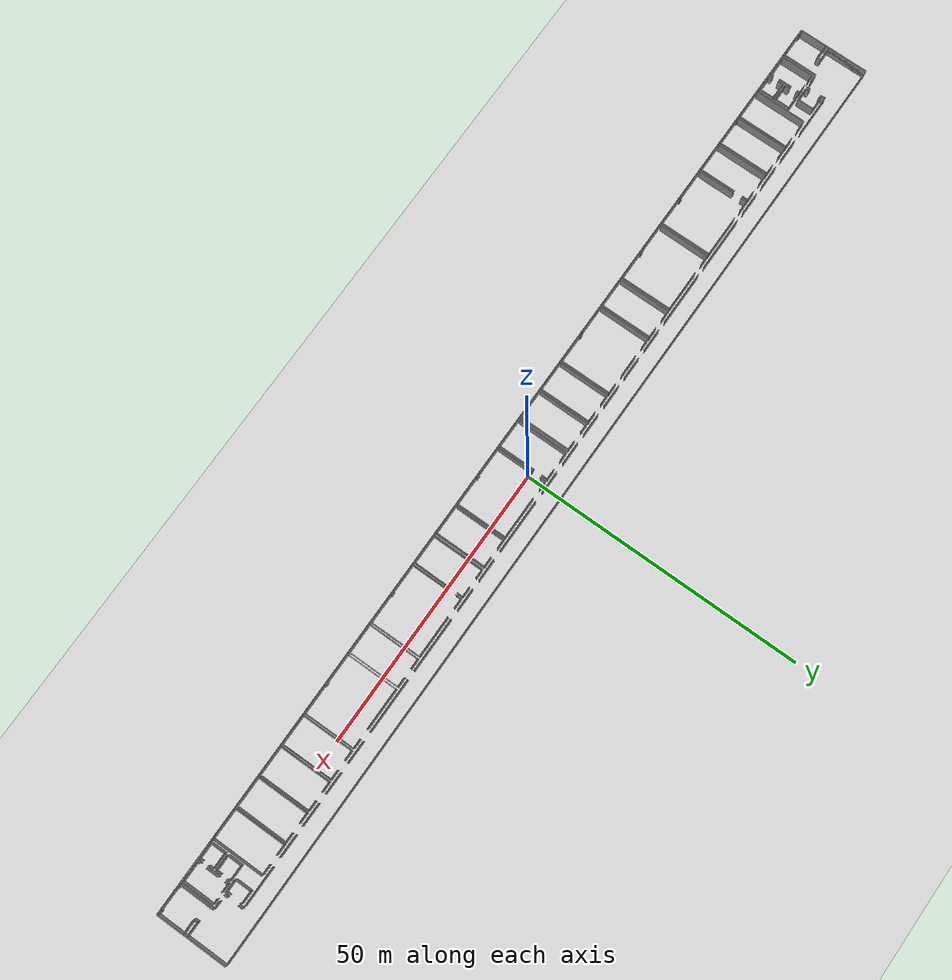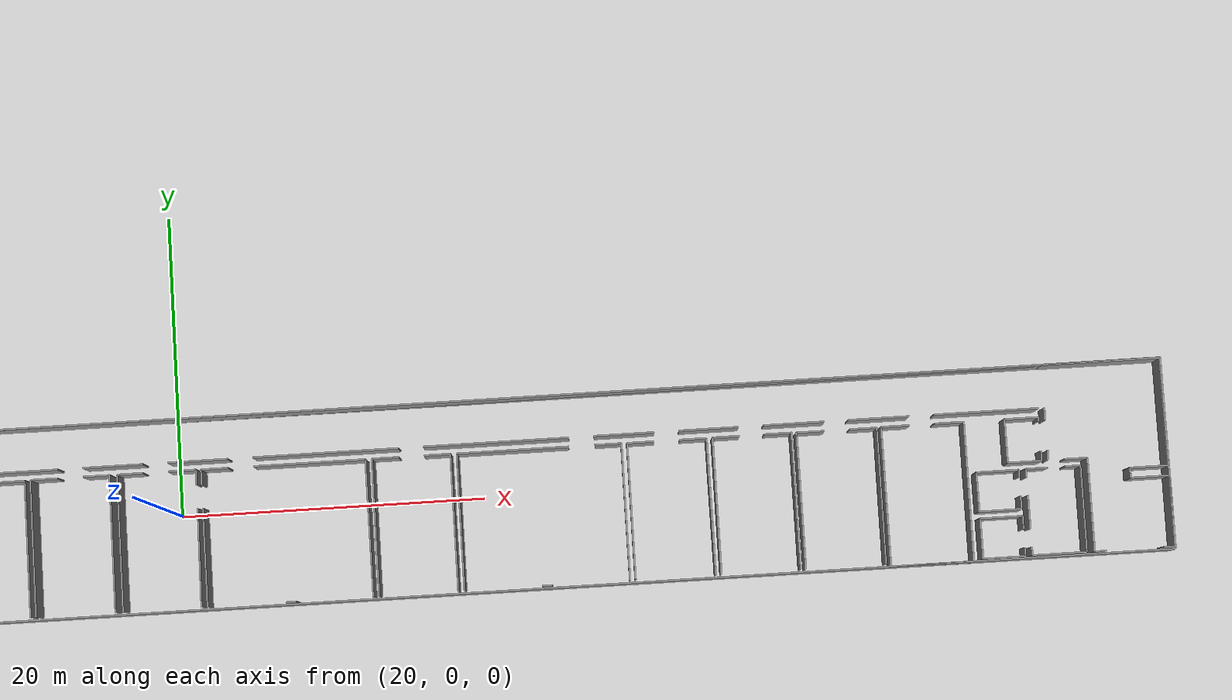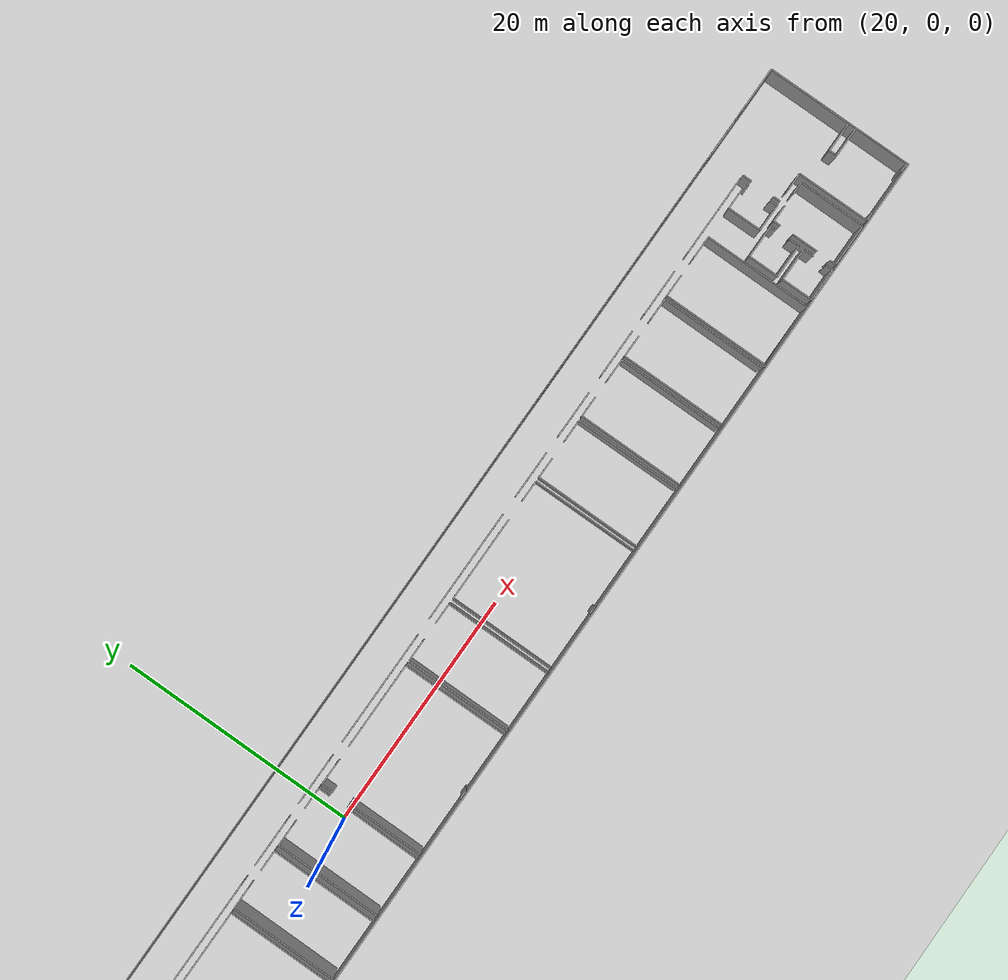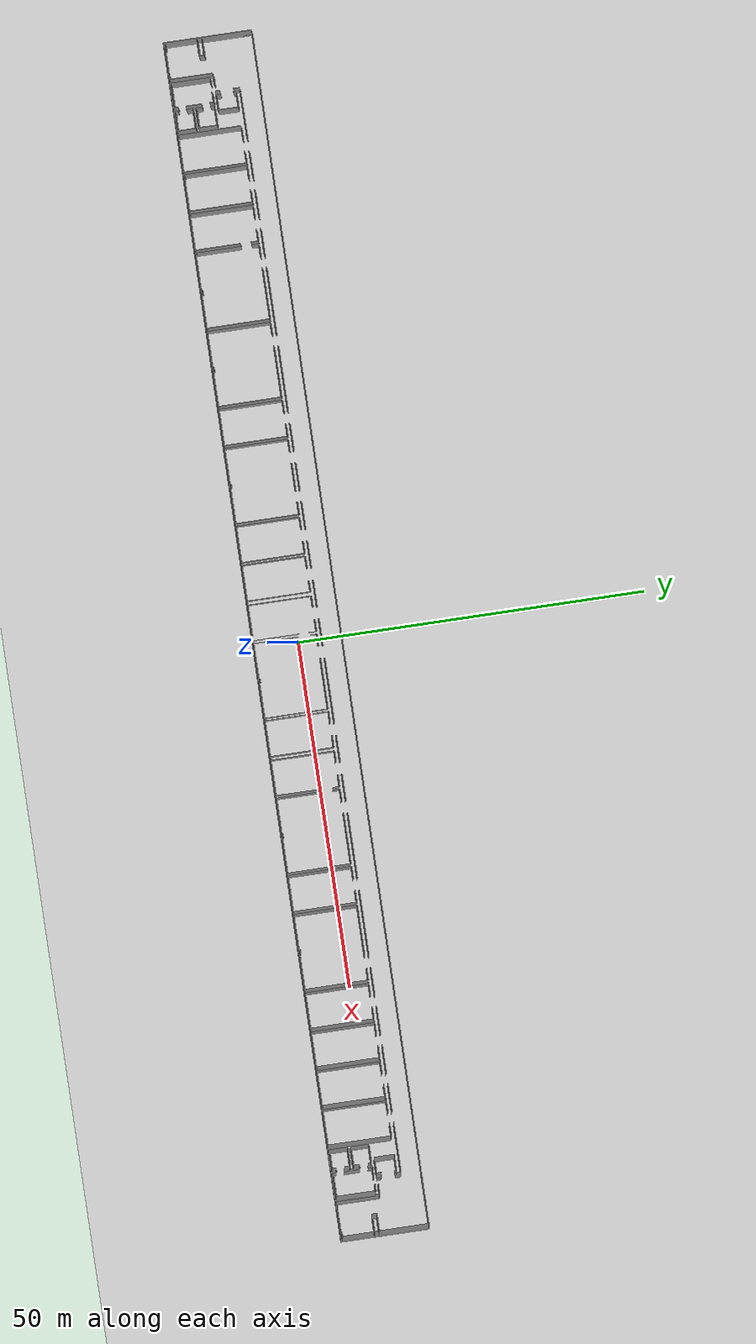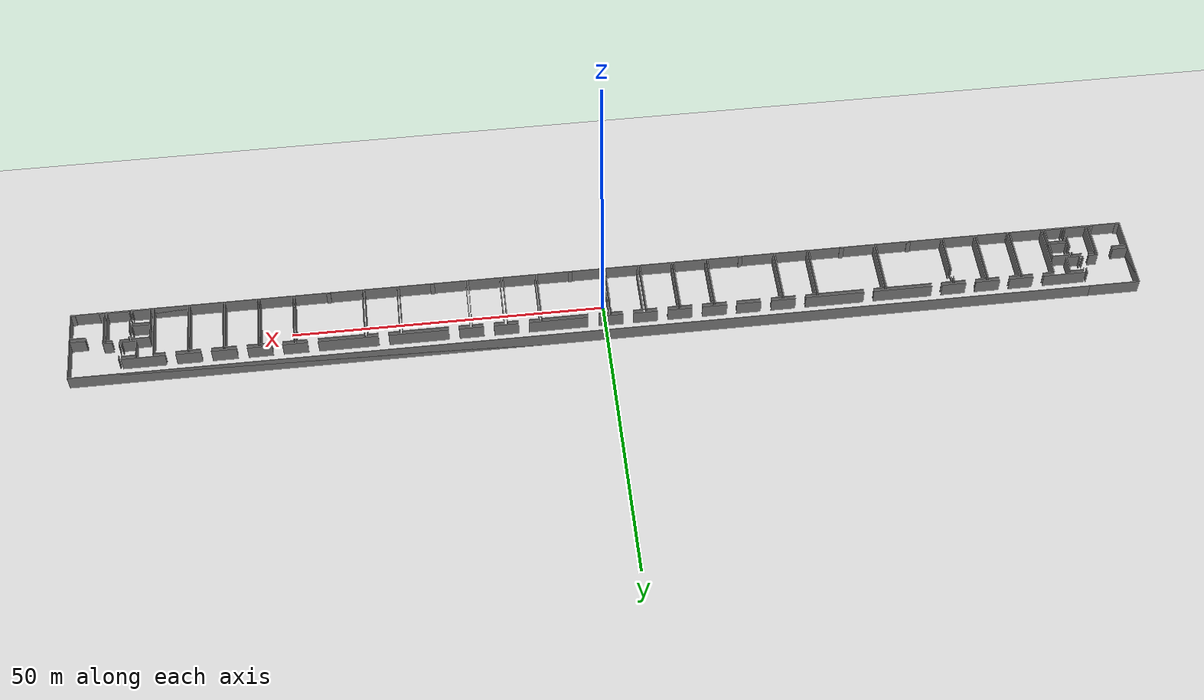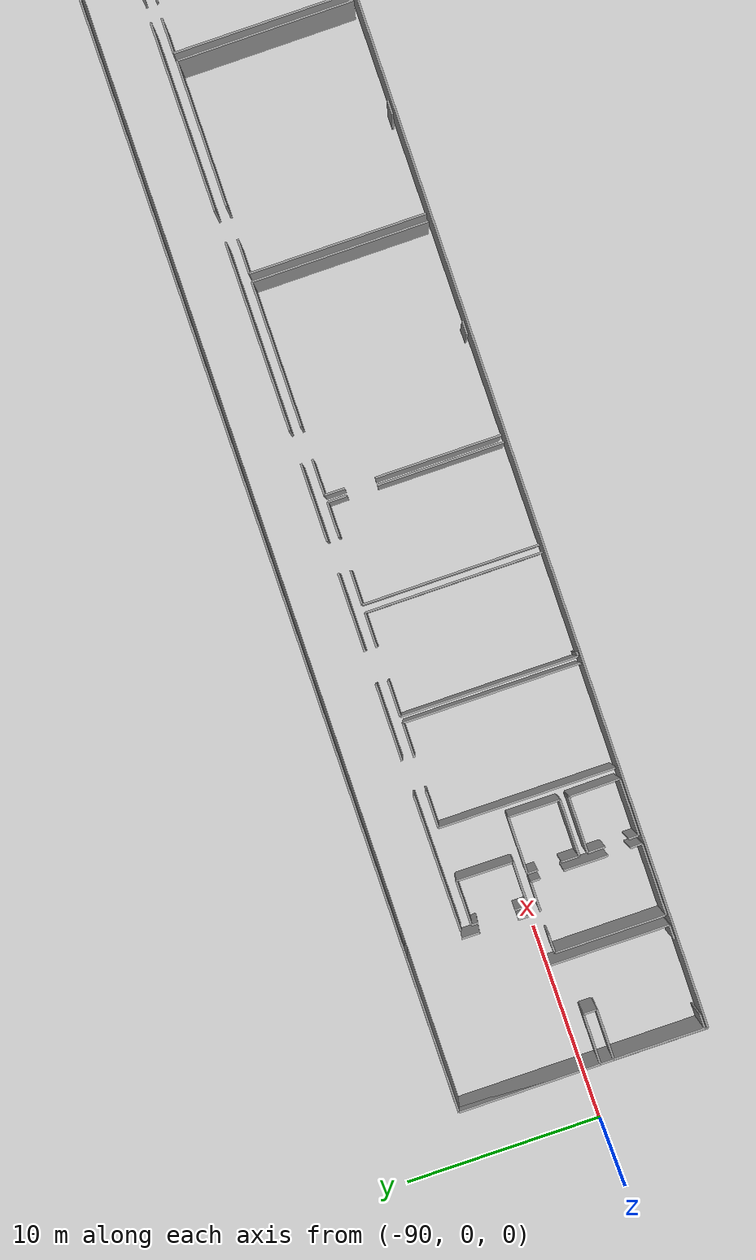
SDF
<sdf version="1.6">
  <world name="default">
    <light name="sun" type="directional">
      <cast_shadows>1</cast_shadows>
      <pose frame="">0 0 10 0 -0 0</pose>
      <diffuse>0.8 0.8 0.8 1</diffuse>
      <specular>0.1 0.1 0.1 1</specular>
      <attenuation>
        <range>1000</range>
        <constant>0.9</constant>
        <linear>0.01</linear>
        <quadratic>0.001</quadratic>
      </attenuation>
      <direction>-0.5 0.5 -1</direction>
    </light>
    <model name="ground_plane">
      <static>1</static>
      <link name="link">
        <collision name="collision">
          <geometry>
            <plane>
              <normal>0 0 1</normal>
              <size>100 100</size>
            </plane>
          </geometry>
          <surface>
            <friction>
              <ode>
                <mu>100</mu>
                <mu2>50</mu2>
              </ode>
              <torsional>
                <ode />
              </torsional>
            </friction>
            <contact>
              <ode />
            </contact>
            <bounce />
          </surface>
          <max_contacts>10</max_contacts>
        </collision>
        <visual name="visual">
          <cast_shadows>0</cast_shadows>
          <geometry>
            <plane>
              <normal>0 0 1</normal>
              <size>100 100</size>
            </plane>
          </geometry>
          <material>
            <script>
              <uri>file://media/materials/scripts/gazebo.material</uri>
              <name>Gazebo/Grey</name>
            </script>
          </material>
        </visual>
        <self_collide>0</self_collide>
        <kinematic>0</kinematic>
        <gravity>1</gravity>
      </link>
    </model>
    <gravity>0 0 -9.8</gravity>
    <magnetic_field>6e-06 2.3e-05 -4.2e-05</magnetic_field>
    <atmosphere type="adiabatic" />
    <physics default="0" name="default_physics" type="ode">
      <max_step_size>0.001</max_step_size>
      <real_time_factor>1</real_time_factor>
      <real_time_update_rate>1000</real_time_update_rate>
    </physics>
    <scene>
      <ambient>0.4 0.4 0.4 1</ambient>
      <background>0.7 0.7 0.7 1</background>
      <shadows>1</shadows>
    </scene>
    <spherical_coordinates>
      <surface_model>EARTH_WGS84</surface_model>
      <latitude_deg>0</latitude_deg>
      <longitude_deg>0</longitude_deg>
      <elevation>0</elevation>
      <heading_deg>0</heading_deg>
    </spherical_coordinates>
  <model name="50015850_PLAN4">
		<static>1</static>
		<link name="Wall_0">
			<collision name="Wall_0_Collision">
				<geometry>
					<box>
						<size>155.389632638 0.1 2.5</size>
					</box>
				</geometry>
				<pose frame="">77.6948163188 0 1.25 0 0 0</pose>
			</collision>
			<visual name="Wall_0_Visual">
				<pose frame="">77.6948163188 0 1.25 0 0 0</pose>
				<geometry>
					<box>
						<size>155.389632638 0.1 2.5</size>
					</box>
				</geometry>
				<material>
					<script>
						<uri>file://media/materials/scripts/gazebo.material</uri>
						<name>Gazebo/Grey</name>
					</script>
					<ambient>1 1 1 1</ambient>
				</material>
			</visual>
			<pose frame="">8.19465769938 -0.0 0 0 0 0.0</pose>
		</link>
		<link name="Wall_1">
			<collision name="Wall_1_Collision">
				<geometry>
					<box>
						<size>6.89321743544 0.1 2.5</size>
					</box>
				</geometry>
				<pose frame="">3.44660871772 0 1.25 0 0 0</pose>
			</collision>
			<visual name="Wall_1_Visual">
				<pose frame="">3.44660871772 0 1.25 0 0 0</pose>
				<geometry>
					<box>
						<size>6.89321743544 0.1 2.5</size>
					</box>
				</geometry>
				<material>
					<script>
						<uri>file://media/materials/scripts/gazebo.material</uri>
						<name>Gazebo/Grey</name>
					</script>
					<ambient>1 1 1 1</ambient>
				</material>
			</visual>
			<pose frame="">163.584290337 -2.85164646913 0 0 0 3.14159265359</pose>
		</link>
		<link name="Wall_2">
			<collision name="Wall_2_Collision">
				<geometry>
					<box>
						<size>4.01091301313 0.1 2.5</size>
					</box>
				</geometry>
				<pose frame="">2.00545650657 0 1.25 0 0 0</pose>
			</collision>
			<visual name="Wall_2_Visual">
				<pose frame="">2.00545650657 0 1.25 0 0 0</pose>
				<geometry>
					<box>
						<size>4.01091301313 0.1 2.5</size>
					</box>
				</geometry>
				<material>
					<script>
						<uri>file://media/materials/scripts/gazebo.material</uri>
						<name>Gazebo/Grey</name>
					</script>
					<ambient>1 1 1 1</ambient>
				</material>
			</visual>
			<pose frame="">155.048029947 -2.85164646913 0 0 0 3.14159265359</pose>
		</link>
		<link name="Wall_3">
			<collision name="Wall_3_Collision">
				<geometry>
					<box>
						<size>4.02207981727 0.1 2.5</size>
					</box>
				</geometry>
				<pose frame="">2.01103990864 0 1.25 0 0 0</pose>
			</collision>
			<visual name="Wall_3_Visual">
				<pose frame="">2.01103990864 0 1.25 0 0 0</pose>
				<geometry>
					<box>
						<size>4.02207981727 0.1 2.5</size>
					</box>
				</geometry>
				<material>
					<script>
						<uri>file://media/materials/scripts/gazebo.material</uri>
						<name>Gazebo/Grey</name>
					</script>
					<ambient>1 1 1 1</ambient>
				</material>
			</visual>
			<pose frame="">149.47503331 -2.85164646913 0 0 0 3.14159265359</pose>
		</link>
		<link name="Wall_4">
			<collision name="Wall_4_Collision">
				<geometry>
					<box>
						<size>3.91777171499 0.1 2.5</size>
					</box>
				</geometry>
				<pose frame="">1.9588858575 0 1.25 0 0 0</pose>
			</collision>
			<visual name="Wall_4_Visual">
				<pose frame="">1.9588858575 0 1.25 0 0 0</pose>
				<geometry>
					<box>
						<size>3.91777171499 0.1 2.5</size>
					</box>
				</geometry>
				<material>
					<script>
						<uri>file://media/materials/scripts/gazebo.material</uri>
						<name>Gazebo/Grey</name>
					</script>
					<ambient>1 1 1 1</ambient>
				</material>
			</visual>
			<pose frame="">143.809910539 -2.85164646913 0 0 0 3.14159265359</pose>
		</link>
		<link name="Wall_5">
			<collision name="Wall_5_Collision">
				<geometry>
					<box>
						<size>3.98731044984 0.1 2.5</size>
					</box>
				</geometry>
				<pose frame="">1.99365522492 0 1.25 0 0 0</pose>
			</collision>
			<visual name="Wall_5_Visual">
				<pose frame="">1.99365522492 0 1.25 0 0 0</pose>
				<geometry>
					<box>
						<size>3.98731044984 0.1 2.5</size>
					</box>
				</geometry>
				<material>
					<script>
						<uri>file://media/materials/scripts/gazebo.material</uri>
						<name>Gazebo/Grey</name>
					</script>
					<ambient>1 1 1 1</ambient>
				</material>
			</visual>
			<pose frame="">138.268891568 -2.85164646913 0 0 0 3.14159265359</pose>
		</link>
		<link name="Wall_6">
			<collision name="Wall_6_Collision">
				<geometry>
					<box>
						<size>9.57705729332 0.1 2.5</size>
					</box>
				</geometry>
				<pose frame="">4.78852864666 0 1.25 0 0 0</pose>
			</collision>
			<visual name="Wall_6_Visual">
				<pose frame="">4.78852864666 0 1.25 0 0 0</pose>
				<geometry>
					<box>
						<size>9.57705729332 0.1 2.5</size>
					</box>
				</geometry>
				<material>
					<script>
						<uri>file://media/materials/scripts/gazebo.material</uri>
						<name>Gazebo/Grey</name>
					</script>
					<ambient>1 1 1 1</ambient>
				</material>
			</visual>
			<pose frame="">132.641329865 -2.85164646913 0 0 0 3.14159265359</pose>
		</link>
		<link name="Wall_7">
			<collision name="Wall_7_Collision">
				<geometry>
					<box>
						<size>9.56233741514 0.1 2.5</size>
					</box>
				</geometry>
				<pose frame="">4.78116870757 0 1.25 0 0 0</pose>
			</collision>
			<visual name="Wall_7_Visual">
				<pose frame="">4.78116870757 0 1.25 0 0 0</pose>
				<geometry>
					<box>
						<size>9.56233741514 0.1 2.5</size>
					</box>
				</geometry>
				<material>
					<script>
						<uri>file://media/materials/scripts/gazebo.material</uri>
						<name>Gazebo/Grey</name>
					</script>
					<ambient>1 1 1 1</ambient>
				</material>
			</visual>
			<pose frame="">121.449146628 -2.85164646913 0 0 0 3.14159265359</pose>
		</link>
		<link name="Wall_8">
			<collision name="Wall_8_Collision">
				<geometry>
					<box>
						<size>3.93249159317 0.1 2.5</size>
					</box>
				</geometry>
				<pose frame="">1.96624579659 0 1.25 0 0 0</pose>
			</collision>
			<visual name="Wall_8_Visual">
				<pose frame="">1.96624579659 0 1.25 0 0 0</pose>
				<geometry>
					<box>
						<size>3.93249159317 0.1 2.5</size>
					</box>
				</geometry>
				<material>
					<script>
						<uri>file://media/materials/scripts/gazebo.material</uri>
						<name>Gazebo/Grey</name>
					</script>
					<ambient>1 1 1 1</ambient>
				</material>
			</visual>
			<pose frame="">110.232599454 -2.85164646913 0 0 0 3.14159265359</pose>
		</link>
		<link name="Wall_9">
			<collision name="Wall_9_Collision">
				<geometry>
					<box>
						<size>3.94924179938 0.1 2.5</size>
					</box>
				</geometry>
				<pose frame="">1.97462089969 0 1.25 0 0 0</pose>
			</collision>
			<visual name="Wall_9_Visual">
				<pose frame="">1.97462089969 0 1.25 0 0 0</pose>
				<geometry>
					<box>
						<size>3.94924179938 0.1 2.5</size>
					</box>
				</geometry>
				<material>
					<script>
						<uri>file://media/materials/scripts/gazebo.material</uri>
						<name>Gazebo/Grey</name>
					</script>
					<ambient>1 1 1 1</ambient>
				</material>
			</visual>
			<pose frame="">104.665947592 -2.85164646913 0 0 0 3.14159265359</pose>
		</link>
		<link name="Wall_10">
			<collision name="Wall_10_Collision">
				<geometry>
					<box>
						<size>9.50929509549 0.1 2.5</size>
					</box>
				</geometry>
				<pose frame="">4.75464754774 0 1.25 0 0 0</pose>
			</collision>
			<visual name="Wall_10_Visual">
				<pose frame="">4.75464754774 0 1.25 0 0 0</pose>
				<geometry>
					<box>
						<size>9.50929509549 0.1 2.5</size>
					</box>
				</geometry>
				<material>
					<script>
						<uri>file://media/materials/scripts/gazebo.material</uri>
						<name>Gazebo/Grey</name>
					</script>
					<ambient>1 1 1 1</ambient>
				</material>
			</visual>
			<pose frame="">99.0693483916 -2.85164646913 0 0 0 3.14159265359</pose>
		</link>
		<link name="Wall_11">
			<collision name="Wall_11_Collision">
				<geometry>
					<box>
						<size>3.95482520145 0.1 2.5</size>
					</box>
				</geometry>
				<pose frame="">1.97741260072 0 1.25 0 0 0</pose>
			</collision>
			<visual name="Wall_11_Visual">
				<pose frame="">1.97741260072 0 1.25 0 0 0</pose>
				<geometry>
					<box>
						<size>3.95482520145 0.1 2.5</size>
					</box>
				</geometry>
				<material>
					<script>
						<uri>file://media/materials/scripts/gazebo.material</uri>
						<name>Gazebo/Grey</name>
					</script>
					<ambient>1 1 1 1</ambient>
				</material>
			</visual>
			<pose frame="">87.8746272445 -2.85164646913 0 0 0 3.14159265359</pose>
		</link>
		<link name="Wall_12">
			<collision name="Wall_12_Collision">
				<geometry>
					<box>
						<size>3.93883636825 0.1 2.5</size>
					</box>
				</geometry>
				<pose frame="">1.96941818413 0 1.25 0 0 0</pose>
			</collision>
			<visual name="Wall_12_Visual">
				<pose frame="">1.96941818413 0 1.25 0 0 0</pose>
				<geometry>
					<box>
						<size>3.93883636825 0.1 2.5</size>
					</box>
				</geometry>
				<material>
					<script>
						<uri>file://media/materials/scripts/gazebo.material</uri>
						<name>Gazebo/Grey</name>
					</script>
					<ambient>1 1 1 1</ambient>
				</material>
			</visual>
			<pose frame="">82.2820887 -2.85164646913 0 0 0 3.14159265359</pose>
		</link>
		<link name="Wall_13">
			<collision name="Wall_13_Collision">
				<geometry>
					<box>
						<size>3.96218514054 0.1 2.5</size>
					</box>
				</geometry>
				<pose frame="">1.98109257027 0 1.25 0 0 0</pose>
			</collision>
			<visual name="Wall_13_Visual">
				<pose frame="">1.98109257027 0 1.25 0 0 0</pose>
				<geometry>
					<box>
						<size>3.96218514054 0.1 2.5</size>
					</box>
				</geometry>
				<material>
					<script>
						<uri>file://media/materials/scripts/gazebo.material</uri>
						<name>Gazebo/Grey</name>
					</script>
					<ambient>1 1 1 1</ambient>
				</material>
			</visual>
			<pose frame="">76.6986866316 -2.85164646913 0 0 0 3.14159265359</pose>
		</link>
		<link name="Wall_14">
			<collision name="Wall_14_Collision">
				<geometry>
					<box>
						<size>4.00482202906 0.1 2.5</size>
					</box>
				</geometry>
				<pose frame="">2.00241101453 0 1.25 0 0 0</pose>
			</collision>
			<visual name="Wall_14_Visual">
				<pose frame="">2.00241101453 0 1.25 0 0 0</pose>
				<geometry>
					<box>
						<size>4.00482202906 0.1 2.5</size>
					</box>
				</geometry>
				<material>
					<script>
						<uri>file://media/materials/scripts/gazebo.material</uri>
						<name>Gazebo/Grey</name>
					</script>
					<ambient>1 1 1 1</ambient>
				</material>
			</visual>
			<pose frame="">71.0906668359 -2.85164646913 0 0 0 3.14159265359</pose>
		</link>
		<link name="Wall_15">
			<collision name="Wall_15_Collision">
				<geometry>
					<box>
						<size>3.95482520145 0.1 2.5</size>
					</box>
				</geometry>
				<pose frame="">1.97741260072 0 1.25 0 0 0</pose>
			</collision>
			<visual name="Wall_15_Visual">
				<pose frame="">1.97741260072 0 1.25 0 0 0</pose>
				<geometry>
					<box>
						<size>3.95482520145 0.1 2.5</size>
					</box>
				</geometry>
				<material>
					<script>
						<uri>file://media/materials/scripts/gazebo.material</uri>
						<name>Gazebo/Grey</name>
					</script>
					<ambient>1 1 1 1</ambient>
				</material>
			</visual>
			<pose frame="">65.5108178415 -2.85164646913 0 0 0 3.14159265359</pose>
		</link>
		<link name="Wall_16">
			<collision name="Wall_16_Collision">
				<geometry>
					<box>
						<size>3.96878370662 0.1 2.5</size>
					</box>
				</geometry>
				<pose frame="">1.98439185331 0 1.25 0 0 0</pose>
			</collision>
			<visual name="Wall_16_Visual">
				<pose frame="">1.98439185331 0 1.25 0 0 0</pose>
				<geometry>
					<box>
						<size>3.96878370662 0.1 2.5</size>
					</box>
				</geometry>
				<material>
					<script>
						<uri>file://media/materials/scripts/gazebo.material</uri>
						<name>Gazebo/Grey</name>
					</script>
					<ambient>1 1 1 1</ambient>
				</material>
			</visual>
			<pose frame="">59.8807182285 -2.85164646913 0 0 0 3.14159265359</pose>
		</link>
		<link name="Wall_17">
			<collision name="Wall_17_Collision">
				<geometry>
					<box>
						<size>9.53340524078 0.1 2.5</size>
					</box>
				</geometry>
				<pose frame="">4.76670262039 0 1.25 0 0 0</pose>
			</collision>
			<visual name="Wall_17_Visual">
				<pose frame="">4.76670262039 0 1.25 0 0 0</pose>
				<geometry>
					<box>
						<size>9.53340524078 0.1 2.5</size>
					</box>
				</geometry>
				<material>
					<script>
						<uri>file://media/materials/scripts/gazebo.material</uri>
						<name>Gazebo/Grey</name>
					</script>
					<ambient>1 1 1 1</ambient>
				</material>
			</visual>
			<pose frame="">54.2506186156 -2.85164646913 0 0 0 3.14159265359</pose>
		</link>
		<link name="Wall_18">
			<collision name="Wall_18_Collision">
				<geometry>
					<box>
						<size>9.56284499714 0.1 2.5</size>
					</box>
				</geometry>
				<pose frame="">4.78142249857 0 1.25 0 0 0</pose>
			</collision>
			<visual name="Wall_18_Visual">
				<pose frame="">4.78142249857 0 1.25 0 0 0</pose>
				<geometry>
					<box>
						<size>9.56284499714 0.1 2.5</size>
					</box>
				</geometry>
				<material>
					<script>
						<uri>file://media/materials/scripts/gazebo.material</uri>
						<name>Gazebo/Grey</name>
					</script>
					<ambient>1 1 1 1</ambient>
				</material>
			</visual>
			<pose frame="">43.1173148912 -2.85164646913 0 0 0 3.14159265359</pose>
		</link>
		<link name="Wall_19">
			<collision name="Wall_19_Collision">
				<geometry>
					<box>
						<size>3.92132478904 0.1 2.5</size>
					</box>
				</geometry>
				<pose frame="">1.96066239452 0 1.25 0 0 0</pose>
			</collision>
			<visual name="Wall_19_Visual">
				<pose frame="">1.96066239452 0 1.25 0 0 0</pose>
				<geometry>
					<box>
						<size>3.92132478904 0.1 2.5</size>
					</box>
				</geometry>
				<material>
					<script>
						<uri>file://media/materials/scripts/gazebo.material</uri>
						<name>Gazebo/Grey</name>
					</script>
					<ambient>1 1 1 1</ambient>
				</material>
			</visual>
			<pose frame="">31.8890933316 -2.85164646913 0 0 0 3.14159265359</pose>
		</link>
		<link name="Wall_20">
			<collision name="Wall_20_Collision">
				<geometry>
					<box>
						<size>3.97817397373 0.1 2.5</size>
					</box>
				</geometry>
				<pose frame="">1.98908698687 0 1.25 0 0 0</pose>
			</collision>
			<visual name="Wall_20_Visual">
				<pose frame="">1.98908698687 0 1.25 0 0 0</pose>
				<geometry>
					<box>
						<size>3.97817397373 0.1 2.5</size>
					</box>
				</geometry>
				<material>
					<script>
						<uri>file://media/materials/scripts/gazebo.material</uri>
						<name>Gazebo/Grey</name>
					</script>
					<ambient>1 1 1 1</ambient>
				</material>
			</visual>
			<pose frame="">26.3490895248 -2.85164646913 0 0 0 3.14159265359</pose>
		</link>
		<link name="Wall_21">
			<collision name="Wall_21_Collision">
				<geometry>
					<box>
						<size>3.88807816763 0.1 2.5</size>
					</box>
				</geometry>
				<pose frame="">1.94403908381 0 1.25 0 0 0</pose>
			</collision>
			<visual name="Wall_21_Visual">
				<pose frame="">1.94403908381 0 1.25 0 0 0</pose>
				<geometry>
					<box>
						<size>3.88807816763 0.1 2.5</size>
					</box>
				</geometry>
				<material>
					<script>
						<uri>file://media/materials/scripts/gazebo.material</uri>
						<name>Gazebo/Grey</name>
					</script>
					<ambient>1 1 1 1</ambient>
				</material>
			</visual>
			<pose frame="">20.7253346869 -2.85164646913 0 0 0 3.14159265359</pose>
		</link>
		<link name="Wall_22">
			<collision name="Wall_22_Collision">
				<geometry>
					<box>
						<size>6.89207662407 0.1 2.5</size>
					</box>
				</geometry>
				<pose frame="">3.44603831203 0 1.25 0 0 0</pose>
			</collision>
			<visual name="Wall_22_Visual">
				<pose frame="">3.44603831203 0 1.25 0 0 0</pose>
				<geometry>
					<box>
						<size>6.89207662407 0.1 2.5</size>
					</box>
				</geometry>
				<material>
					<script>
						<uri>file://media/materials/scripts/gazebo.material</uri>
						<name>Gazebo/Grey</name>
					</script>
					<ambient>1 1 1 1</ambient>
				</material>
			</visual>
			<pose frame="">15.0866061798 -2.85164646913 0 0 0 -3.13549462931</pose>
		</link>
		<link name="Wall_23">
			<collision name="Wall_23_Collision">
				<geometry>
					<box>
						<size>0.721781612842 0.1 2.5</size>
					</box>
				</geometry>
				<pose frame="">0.360890806421 0 1.25 0 0 0</pose>
			</collision>
			<visual name="Wall_23_Visual">
				<pose frame="">0.360890806421 0 1.25 0 0 0</pose>
				<geometry>
					<box>
						<size>0.721781612842 0.1 2.5</size>
					</box>
				</geometry>
				<material>
					<script>
						<uri>file://media/materials/scripts/gazebo.material</uri>
						<name>Gazebo/Grey</name>
					</script>
					<ambient>1 1 1 1</ambient>
				</material>
			</visual>
			<pose frame="">5.24763657128 -12.4594886111 0 0 0 3.14159265359</pose>
		</link>
		<link name="Wall_24">
			<collision name="Wall_24_Collision">
				<geometry>
					<box>
						<size>0.714929255758 0.1 2.5</size>
					</box>
				</geometry>
				<pose frame="">0.357464627879 0 1.25 0 0 0</pose>
			</collision>
			<visual name="Wall_24_Visual">
				<pose frame="">0.357464627879 0 1.25 0 0 0</pose>
				<geometry>
					<box>
						<size>0.714929255758 0.1 2.5</size>
					</box>
				</geometry>
				<material>
					<script>
						<uri>file://media/materials/scripts/gazebo.material</uri>
						<name>Gazebo/Grey</name>
					</script>
					<ambient>1 1 1 1</ambient>
				</material>
			</visual>
			<pose frame="">0.730410506948 -12.4594886111 0 0 0 3.14159265359</pose>
		</link>
		<link name="Wall_25">
			<collision name="Wall_25_Collision">
				<geometry>
					<box>
						<size>4.60823551805 0.1 2.5</size>
					</box>
				</geometry>
				<pose frame="">2.30411775903 0 1.25 0 0 0</pose>
			</collision>
			<visual name="Wall_25_Visual">
				<pose frame="">2.30411775903 0 1.25 0 0 0</pose>
				<geometry>
					<box>
						<size>4.60823551805 0.1 2.5</size>
					</box>
				</geometry>
				<material>
					<script>
						<uri>file://media/materials/scripts/gazebo.material</uri>
						<name>Gazebo/Grey</name>
					</script>
					<ambient>1 1 1 1</ambient>
				</material>
			</visual>
			<pose frame="">0.0154812511896 -12.4594886111 0 0 0 1.57079632679</pose>
		</link>
		<link name="Wall_26">
			<collision name="Wall_26_Collision">
				<geometry>
					<box>
						<size>2.51303851278 0.1 2.5</size>
					</box>
				</geometry>
				<pose frame="">1.25651925639 0 1.25 0 0 0</pose>
			</collision>
			<visual name="Wall_26_Visual">
				<pose frame="">1.25651925639 0 1.25 0 0 0</pose>
				<geometry>
					<box>
						<size>2.51303851278 0.1 2.5</size>
					</box>
				</geometry>
				<material>
					<script>
						<uri>file://media/materials/scripts/gazebo.material</uri>
						<name>Gazebo/Grey</name>
					</script>
					<ambient>1 1 1 1</ambient>
				</material>
			</visual>
			<pose frame="">0.0154812511896 -7.85125309308 0 0 0 0.0</pose>
		</link>
		<link name="Wall_27">
			<collision name="Wall_27_Collision">
				<geometry>
					<box>
						<size>0.677418945498 0.1 2.5</size>
					</box>
				</geometry>
				<pose frame="">0.338709472749 0 1.25 0 0 0</pose>
			</collision>
			<visual name="Wall_27_Visual">
				<pose frame="">0.338709472749 0 1.25 0 0 0</pose>
				<geometry>
					<box>
						<size>0.677418945498 0.1 2.5</size>
					</box>
				</geometry>
				<material>
					<script>
						<uri>file://media/materials/scripts/gazebo.material</uri>
						<name>Gazebo/Grey</name>
					</script>
					<ambient>1 1 1 1</ambient>
				</material>
			</visual>
			<pose frame="">2.52851976397 -7.85125309308 0 0 0 1.57079632679</pose>
		</link>
		<link name="Wall_28">
			<collision name="Wall_28_Collision">
				<geometry>
					<box>
						<size>2.52851976397 0.1 2.5</size>
					</box>
				</geometry>
				<pose frame="">1.26425988199 0 1.25 0 0 0</pose>
			</collision>
			<visual name="Wall_28_Visual">
				<pose frame="">1.26425988199 0 1.25 0 0 0</pose>
				<geometry>
					<box>
						<size>2.52851976397 0.1 2.5</size>
					</box>
				</geometry>
				<material>
					<script>
						<uri>file://media/materials/scripts/gazebo.material</uri>
						<name>Gazebo/Grey</name>
					</script>
					<ambient>1 1 1 1</ambient>
				</material>
			</visual>
			<pose frame="">2.52851976397 -7.17383414758 0 0 0 3.14159265359</pose>
		</link>
		<link name="Wall_29">
			<collision name="Wall_29_Collision">
				<geometry>
					<box>
						<size>7.1673117188 0.1 2.5</size>
					</box>
				</geometry>
				<pose frame="">3.5836558594 0 1.25 0 0 0</pose>
			</collision>
			<visual name="Wall_29_Visual">
				<pose frame="">3.5836558594 0 1.25 0 0 0</pose>
				<geometry>
					<box>
						<size>7.1673117188 0.1 2.5</size>
					</box>
				</geometry>
				<material>
					<script>
						<uri>file://media/materials/scripts/gazebo.material</uri>
						<name>Gazebo/Grey</name>
					</script>
					<ambient>1 1 1 1</ambient>
				</material>
			</visual>
			<pose frame="">0.0 -7.17383414758 0 0 0 1.57079632679</pose>
		</link>
		<link name="Wall_30">
			<collision name="Wall_30_Collision">
				<geometry>
					<box>
						<size>7.83858892202 0.1 2.5</size>
					</box>
				</geometry>
				<pose frame="">3.91929446101 0 1.25 0 0 0</pose>
			</collision>
			<visual name="Wall_30_Visual">
				<pose frame="">3.91929446101 0 1.25 0 0 0</pose>
				<geometry>
					<box>
						<size>7.83858892202 0.1 2.5</size>
					</box>
				</geometry>
				<material>
					<script>
						<uri>file://media/materials/scripts/gazebo.material</uri>
						<name>Gazebo/Grey</name>
					</script>
					<ambient>1 1 1 1</ambient>
				</material>
			</visual>
			<pose frame="">0.0 -0.0065224287799 0 0 0 0.0</pose>
		</link>
		<link name="Wall_31">
			<collision name="Wall_31_Collision">
				<geometry>
					<box>
						<size>0.910678256456 0.1 2.5</size>
					</box>
				</geometry>
				<pose frame="">0.455339128228 0 1.25 0 0 0</pose>
			</collision>
			<visual name="Wall_31_Visual">
				<pose frame="">0.455339128228 0 1.25 0 0 0</pose>
				<geometry>
					<box>
						<size>0.910678256456 0.1 2.5</size>
					</box>
				</geometry>
				<material>
					<script>
						<uri>file://media/materials/scripts/gazebo.material</uri>
						<name>Gazebo/Grey</name>
					</script>
					<ambient>1 1 1 1</ambient>
				</material>
			</visual>
			<pose frame="">7.83858892202 -2.81982107734 0 0 0 -1.57079632679</pose>
		</link>
		<link name="Wall_32">
			<collision name="Wall_32_Collision">
				<geometry>
					<box>
						<size>0.658435378466 0.1 2.5</size>
					</box>
				</geometry>
				<pose frame="">0.329217689233 0 1.25 0 0 0</pose>
			</collision>
			<visual name="Wall_32_Visual">
				<pose frame="">0.329217689233 0 1.25 0 0 0</pose>
				<geometry>
					<box>
						<size>0.658435378466 0.1 2.5</size>
					</box>
				</geometry>
				<material>
					<script>
						<uri>file://media/materials/scripts/gazebo.material</uri>
						<name>Gazebo/Grey</name>
					</script>
					<ambient>1 1 1 1</ambient>
				</material>
			</visual>
			<pose frame="">7.83858892202 -5.66999555866 0 0 0 -1.57079632679</pose>
		</link>
		<link name="Wall_33">
			<collision name="Wall_33_Collision">
				<geometry>
					<box>
						<size>1.469449908 0.1 2.5</size>
					</box>
				</geometry>
				<pose frame="">0.734724954 0 1.25 0 0 0</pose>
			</collision>
			<visual name="Wall_33_Visual">
				<pose frame="">0.734724954 0 1.25 0 0 0</pose>
				<geometry>
					<box>
						<size>1.469449908 0.1 2.5</size>
					</box>
				</geometry>
				<material>
					<script>
						<uri>file://media/materials/scripts/gazebo.material</uri>
						<name>Gazebo/Grey</name>
					</script>
					<ambient>1 1 1 1</ambient>
				</material>
			</visual>
			<pose frame="">6.73612080452 -6.32843093712 0 0 0 3.14159265359</pose>
		</link>
		<link name="Wall_34">
			<collision name="Wall_34_Collision">
				<geometry>
					<box>
						<size>6.13108722067 0.1 2.5</size>
					</box>
				</geometry>
				<pose frame="">3.06554361034 0 1.25 0 0 0</pose>
			</collision>
			<visual name="Wall_34_Visual">
				<pose frame="">3.06554361034 0 1.25 0 0 0</pose>
				<geometry>
					<box>
						<size>6.13108722067 0.1 2.5</size>
					</box>
				</geometry>
				<material>
					<script>
						<uri>file://media/materials/scripts/gazebo.material</uri>
						<name>Gazebo/Grey</name>
					</script>
					<ambient>1 1 1 1</ambient>
				</material>
			</visual>
			<pose frame="">5.26667089652 -6.32843093712 0 0 0 -1.57390089131</pose>
		</link>
		<link name="Wall_35">
			<collision name="Wall_35_Collision">
				<geometry>
					<box>
						<size>2.21635683015 0.1 2.5</size>
					</box>
				</geometry>
				<pose frame="">1.10817841508 0 1.25 0 0 0</pose>
			</collision>
			<visual name="Wall_35_Visual">
				<pose frame="">1.10817841508 0 1.25 0 0 0</pose>
				<geometry>
					<box>
						<size>2.21635683015 0.1 2.5</size>
					</box>
				</geometry>
				<material>
					<script>
						<uri>file://media/materials/scripts/gazebo.material</uri>
						<name>Gazebo/Grey</name>
					</script>
					<ambient>1 1 1 1</ambient>
				</material>
			</visual>
			<pose frame="">10.5247128989 -6.33089270985 0 0 0 3.14159265359</pose>
		</link>
		<link name="Wall_36">
			<collision name="Wall_36_Collision">
				<geometry>
					<box>
						<size>0.669297633399 0.1 2.5</size>
					</box>
				</geometry>
				<pose frame="">0.334648816699 0 1.25 0 0 0</pose>
			</collision>
			<visual name="Wall_36_Visual">
				<pose frame="">0.334648816699 0 1.25 0 0 0</pose>
				<geometry>
					<box>
						<size>0.669297633399 0.1 2.5</size>
					</box>
				</geometry>
				<material>
					<script>
						<uri>file://media/materials/scripts/gazebo.material</uri>
						<name>Gazebo/Grey</name>
					</script>
					<ambient>1 1 1 1</ambient>
				</material>
			</visual>
			<pose frame="">8.30835606878 -6.33089270985 0 0 0 1.57079632679</pose>
		</link>
		<link name="Wall_37">
			<collision name="Wall_37_Collision">
				<geometry>
					<box>
						<size>0.33391282279 0.1 2.5</size>
					</box>
				</geometry>
				<pose frame="">0.166956411395 0 1.25 0 0 0</pose>
			</collision>
			<visual name="Wall_37_Visual">
				<pose frame="">0.166956411395 0 1.25 0 0 0</pose>
				<geometry>
					<box>
						<size>0.33391282279 0.1 2.5</size>
					</box>
				</geometry>
				<material>
					<script>
						<uri>file://media/materials/scripts/gazebo.material</uri>
						<name>Gazebo/Grey</name>
					</script>
					<ambient>1 1 1 1</ambient>
				</material>
			</visual>
			<pose frame="">8.30835606878 -3.79633272001 0 0 0 1.57079632679</pose>
		</link>
		<link name="Wall_38">
			<collision name="Wall_38_Collision">
				<geometry>
					<box>
						<size>2.23437599137 0.1 2.5</size>
					</box>
				</geometry>
				<pose frame="">1.11718799569 0 1.25 0 0 0</pose>
			</collision>
			<visual name="Wall_38_Visual">
				<pose frame="">1.11718799569 0 1.25 0 0 0</pose>
				<geometry>
					<box>
						<size>2.23437599137 0.1 2.5</size>
					</box>
				</geometry>
				<material>
					<script>
						<uri>file://media/materials/scripts/gazebo.material</uri>
						<name>Gazebo/Grey</name>
					</script>
					<ambient>1 1 1 1</ambient>
				</material>
			</visual>
			<pose frame="">8.30835606878 -3.46241989721 0 0 0 0.0</pose>
		</link>
		<link name="Wall_39">
			<collision name="Wall_39_Collision">
				<geometry>
					<box>
						<size>2.86852940843 0.1 2.5</size>
					</box>
				</geometry>
				<pose frame="">1.43426470421 0 1.25 0 0 0</pose>
			</collision>
			<visual name="Wall_39_Visual">
				<pose frame="">1.43426470421 0 1.25 0 0 0</pose>
				<geometry>
					<box>
						<size>2.86852940843 0.1 2.5</size>
					</box>
				</geometry>
				<material>
					<script>
						<uri>file://media/materials/scripts/gazebo.material</uri>
						<name>Gazebo/Grey</name>
					</script>
					<ambient>1 1 1 1</ambient>
				</material>
			</visual>
			<pose frame="">10.5427320601 -3.46241989721 0 0 0 -1.57707804023</pose>
		</link>
		<link name="Wall_40">
			<collision name="Wall_40_Collision">
				<geometry>
					<box>
						<size>3.6160142123 0.1 2.5</size>
					</box>
				</geometry>
				<pose frame="">1.80800710615 0 1.25 0 0 0</pose>
			</collision>
			<visual name="Wall_40_Visual">
				<pose frame="">1.80800710615 0 1.25 0 0 0</pose>
				<geometry>
					<box>
						<size>3.6160142123 0.1 2.5</size>
					</box>
				</geometry>
				<material>
					<script>
						<uri>file://media/materials/scripts/gazebo.material</uri>
						<name>Gazebo/Grey</name>
					</script>
					<ambient>1 1 1 1</ambient>
				</material>
			</visual>
			<pose frame="">9.36920246177 -12.4691326692 0 0 0 3.14159265359</pose>
		</link>
		<link name="Wall_41">
			<collision name="Wall_41_Collision">
				<geometry>
					<box>
						<size>5.65111350803 0.1 2.5</size>
					</box>
				</geometry>
				<pose frame="">2.82555675401 0 1.25 0 0 0</pose>
			</collision>
			<visual name="Wall_41_Visual">
				<pose frame="">2.82555675401 0 1.25 0 0 0</pose>
				<geometry>
					<box>
						<size>5.65111350803 0.1 2.5</size>
					</box>
				</geometry>
				<material>
					<script>
						<uri>file://media/materials/scripts/gazebo.material</uri>
						<name>Gazebo/Grey</name>
					</script>
					<ambient>1 1 1 1</ambient>
				</material>
			</visual>
			<pose frame="">5.75318824948 -12.4691326692 0 0 0 1.57079632679</pose>
		</link>
		<link name="Wall_42">
			<collision name="Wall_42_Collision">
				<geometry>
					<box>
						<size>0.924560624326 0.1 2.5</size>
					</box>
				</geometry>
				<pose frame="">0.462280312163 0 1.25 0 0 0</pose>
			</collision>
			<visual name="Wall_42_Visual">
				<pose frame="">0.462280312163 0 1.25 0 0 0</pose>
				<geometry>
					<box>
						<size>0.924560624326 0.1 2.5</size>
					</box>
				</geometry>
				<material>
					<script>
						<uri>file://media/materials/scripts/gazebo.material</uri>
						<name>Gazebo/Grey</name>
					</script>
					<ambient>1 1 1 1</ambient>
				</material>
			</visual>
			<pose frame="">5.75318824948 -6.81801916122 0 0 0 0.0</pose>
		</link>
		<link name="Wall_43">
			<collision name="Wall_43_Collision">
				<geometry>
					<box>
						<size>1.50041241038 0.1 2.5</size>
					</box>
				</geometry>
				<pose frame="">0.75020620519 0 1.25 0 0 0</pose>
			</collision>
			<visual name="Wall_43_Visual">
				<pose frame="">0.75020620519 0 1.25 0 0 0</pose>
				<geometry>
					<box>
						<size>1.50041241038 0.1 2.5</size>
					</box>
				</geometry>
				<material>
					<script>
						<uri>file://media/materials/scripts/gazebo.material</uri>
						<name>Gazebo/Grey</name>
					</script>
					<ambient>1 1 1 1</ambient>
				</material>
			</visual>
			<pose frame="">7.8530550092 -6.81801916122 0 0 0 0.0</pose>
		</link>
		<link name="Wall_44">
			<collision name="Wall_44_Collision">
				<geometry>
					<box>
						<size>0.498420151006 0.1 2.5</size>
					</box>
				</geometry>
				<pose frame="">0.249210075503 0 1.25 0 0 0</pose>
			</collision>
			<visual name="Wall_44_Visual">
				<pose frame="">0.249210075503 0 1.25 0 0 0</pose>
				<geometry>
					<box>
						<size>0.498420151006 0.1 2.5</size>
					</box>
				</geometry>
				<material>
					<script>
						<uri>file://media/materials/scripts/gazebo.material</uri>
						<name>Gazebo/Grey</name>
					</script>
					<ambient>1 1 1 1</ambient>
				</material>
			</visual>
			<pose frame="">9.35346741958 -6.81801916122 0 0 0 -1.57079632679</pose>
		</link>
		<link name="Wall_45">
			<collision name="Wall_45_Collision">
				<geometry>
					<box>
						<size>2.25099930207 0.1 2.5</size>
					</box>
				</geometry>
				<pose frame="">1.12549965104 0 1.25 0 0 0</pose>
			</collision>
			<visual name="Wall_45_Visual">
				<pose frame="">1.12549965104 0 1.25 0 0 0</pose>
				<geometry>
					<box>
						<size>2.25099930207 0.1 2.5</size>
					</box>
				</geometry>
				<material>
					<script>
						<uri>file://media/materials/scripts/gazebo.material</uri>
						<name>Gazebo/Grey</name>
					</script>
					<ambient>1 1 1 1</ambient>
				</material>
			</visual>
			<pose frame="">9.35346741958 -8.49235454603 0 0 0 -1.57079632679</pose>
		</link>
		<link name="Wall_46">
			<collision name="Wall_46_Collision">
				<geometry>
					<box>
						<size>0.607271969239 0.1 2.5</size>
					</box>
				</geometry>
				<pose frame="">0.30363598462 0 1.25 0 0 0</pose>
			</collision>
			<visual name="Wall_46_Visual">
				<pose frame="">0.30363598462 0 1.25 0 0 0</pose>
				<geometry>
					<box>
						<size>0.607271969239 0.1 2.5</size>
					</box>
				</geometry>
				<material>
					<script>
						<uri>file://media/materials/scripts/gazebo.material</uri>
						<name>Gazebo/Grey</name>
					</script>
					<ambient>1 1 1 1</ambient>
				</material>
			</visual>
			<pose frame="">9.35346741958 -11.8620645898 0 0 0 -1.54488239659</pose>
		</link>
		<link name="Wall_47">
			<collision name="Wall_47_Collision">
				<geometry>
					<box>
						<size>2.84575851786 0.1 2.5</size>
					</box>
				</geometry>
				<pose frame="">1.42287925893 0 1.25 0 0 0</pose>
			</collision>
			<visual name="Wall_47_Visual">
				<pose frame="">1.42287925893 0 1.25 0 0 0</pose>
				<geometry>
					<box>
						<size>2.84575851786 0.1 2.5</size>
					</box>
				</geometry>
				<material>
					<script>
						<uri>file://media/materials/scripts/gazebo.material</uri>
						<name>Gazebo/Grey</name>
					</script>
					<ambient>1 1 1 1</ambient>
				</material>
			</visual>
			<pose frame="">12.6248334497 -9.42300615443 0 0 0 3.14159265359</pose>
		</link>
		<link name="Wall_48">
			<collision name="Wall_48_Collision">
				<geometry>
					<box>
						<size>0.904308102278 0.1 2.5</size>
					</box>
				</geometry>
				<pose frame="">0.452154051139 0 1.25 0 0 0</pose>
			</collision>
			<visual name="Wall_48_Visual">
				<pose frame="">0.452154051139 0 1.25 0 0 0</pose>
				<geometry>
					<box>
						<size>0.904308102278 0.1 2.5</size>
					</box>
				</geometry>
				<material>
					<script>
						<uri>file://media/materials/scripts/gazebo.material</uri>
						<name>Gazebo/Grey</name>
					</script>
					<ambient>1 1 1 1</ambient>
				</material>
			</visual>
			<pose frame="">9.77907493179 -9.42300615443 0 0 0 1.57079632679</pose>
		</link>
		<link name="Wall_49">
			<collision name="Wall_49_Collision">
				<geometry>
					<box>
						<size>0.524738278028 0.1 2.5</size>
					</box>
				</geometry>
				<pose frame="">0.262369139014 0 1.25 0 0 0</pose>
			</collision>
			<visual name="Wall_49_Visual">
				<pose frame="">0.262369139014 0 1.25 0 0 0</pose>
				<geometry>
					<box>
						<size>0.524738278028 0.1 2.5</size>
					</box>
				</geometry>
				<material>
					<script>
						<uri>file://media/materials/scripts/gazebo.material</uri>
						<name>Gazebo/Grey</name>
					</script>
					<ambient>1 1 1 1</ambient>
				</material>
			</visual>
			<pose frame="">9.77907493179 -7.32648943595 0 0 0 1.57079632679</pose>
		</link>
		<link name="Wall_50">
			<collision name="Wall_50_Collision">
				<geometry>
					<box>
						<size>2.86276251507 0.1 2.5</size>
					</box>
				</geometry>
				<pose frame="">1.43138125753 0 1.25 0 0 0</pose>
			</collision>
			<visual name="Wall_50_Visual">
				<pose frame="">1.43138125753 0 1.25 0 0 0</pose>
				<geometry>
					<box>
						<size>2.86276251507 0.1 2.5</size>
					</box>
				</geometry>
				<material>
					<script>
						<uri>file://media/materials/scripts/gazebo.material</uri>
						<name>Gazebo/Grey</name>
					</script>
					<ambient>1 1 1 1</ambient>
				</material>
			</visual>
			<pose frame="">9.77907493179 -6.80175115792 0 0 0 0.0</pose>
		</link>
		<link name="Wall_51">
			<collision name="Wall_51_Collision">
				<geometry>
					<box>
						<size>2.62131014812 0.1 2.5</size>
					</box>
				</geometry>
				<pose frame="">1.31065507406 0 1.25 0 0 0</pose>
			</collision>
			<visual name="Wall_51_Visual">
				<pose frame="">1.31065507406 0 1.25 0 0 0</pose>
				<geometry>
					<box>
						<size>2.62131014812 0.1 2.5</size>
					</box>
				</geometry>
				<material>
					<script>
						<uri>file://media/materials/scripts/gazebo.material</uri>
						<name>Gazebo/Grey</name>
					</script>
					<ambient>1 1 1 1</ambient>
				</material>
			</visual>
			<pose frame="">12.6418374469 -6.80175115792 0 0 0 -1.57728320378</pose>
		</link>
		<link name="Wall_52">
			<collision name="Wall_52_Collision">
				<geometry>
					<box>
						<size>2.86580800711 0.1 2.5</size>
					</box>
				</geometry>
				<pose frame="">1.43290400355 0 1.25 0 0 0</pose>
			</collision>
			<visual name="Wall_52_Visual">
				<pose frame="">1.43290400355 0 1.25 0 0 0</pose>
				<geometry>
					<box>
						<size>2.86580800711 0.1 2.5</size>
					</box>
				</geometry>
				<material>
					<script>
						<uri>file://media/materials/scripts/gazebo.material</uri>
						<name>Gazebo/Grey</name>
					</script>
					<ambient>1 1 1 1</ambient>
				</material>
			</visual>
			<pose frame="">12.653258042 -12.4643106402 0 0 0 3.14159265359</pose>
		</link>
		<link name="Wall_53">
			<collision name="Wall_53_Collision">
				<geometry>
					<box>
						<size>0.535752807563 0.1 2.5</size>
					</box>
				</geometry>
				<pose frame="">0.267876403781 0 1.25 0 0 0</pose>
			</collision>
			<visual name="Wall_53_Visual">
				<pose frame="">0.267876403781 0 1.25 0 0 0</pose>
				<geometry>
					<box>
						<size>0.535752807563 0.1 2.5</size>
					</box>
				</geometry>
				<material>
					<script>
						<uri>file://media/materials/scripts/gazebo.material</uri>
						<name>Gazebo/Grey</name>
					</script>
					<ambient>1 1 1 1</ambient>
				</material>
			</visual>
			<pose frame="">9.7874500349 -12.4643106402 0 0 0 1.57079632679</pose>
		</link>
		<link name="Wall_54">
			<collision name="Wall_54_Collision">
				<geometry>
					<box>
						<size>0.88735486327 0.1 2.5</size>
					</box>
				</geometry>
				<pose frame="">0.443677431635 0 1.25 0 0 0</pose>
			</collision>
			<visual name="Wall_54_Visual">
				<pose frame="">0.443677431635 0 1.25 0 0 0</pose>
				<geometry>
					<box>
						<size>0.88735486327 0.1 2.5</size>
					</box>
				</geometry>
				<material>
					<script>
						<uri>file://media/materials/scripts/gazebo.material</uri>
						<name>Gazebo/Grey</name>
					</script>
					<ambient>1 1 1 1</ambient>
				</material>
			</visual>
			<pose frame="">9.7874500349 -10.7517289512 0 0 0 1.57079632679</pose>
		</link>
		<link name="Wall_55">
			<collision name="Wall_55_Collision">
				<geometry>
					<box>
						<size>2.83535308673 0.1 2.5</size>
					</box>
				</geometry>
				<pose frame="">1.41767654337 0 1.25 0 0 0</pose>
			</collision>
			<visual name="Wall_55_Visual">
				<pose frame="">1.41767654337 0 1.25 0 0 0</pose>
				<geometry>
					<box>
						<size>2.83535308673 0.1 2.5</size>
					</box>
				</geometry>
				<material>
					<script>
						<uri>file://media/materials/scripts/gazebo.material</uri>
						<name>Gazebo/Grey</name>
					</script>
					<ambient>1 1 1 1</ambient>
				</material>
			</visual>
			<pose frame="">9.7874500349 -9.86437408794 0 0 0 0.0</pose>
		</link>
		<link name="Wall_56">
			<collision name="Wall_56_Collision">
				<geometry>
					<box>
						<size>2.60011491629 0.1 2.5</size>
					</box>
				</geometry>
				<pose frame="">1.30005745814 0 1.25 0 0 0</pose>
			</collision>
			<visual name="Wall_56_Visual">
				<pose frame="">1.30005745814 0 1.25 0 0 0</pose>
				<geometry>
					<box>
						<size>2.60011491629 0.1 2.5</size>
					</box>
				</geometry>
				<material>
					<script>
						<uri>file://media/materials/scripts/gazebo.material</uri>
						<name>Gazebo/Grey</name>
					</script>
					<ambient>1 1 1 1</ambient>
				</material>
			</visual>
			<pose frame="">12.6228031216 -9.86437408794 0 0 0 -1.55908314574</pose>
		</link>
		<link name="Wall_57">
			<collision name="Wall_57_Collision">
				<geometry>
					<box>
						<size>0.104815684284 0.1 2.5</size>
					</box>
				</geometry>
				<pose frame="">0.052407842142 0 1.25 0 0 0</pose>
			</collision>
			<visual name="Wall_57_Visual">
				<pose frame="">0.052407842142 0 1.25 0 0 0</pose>
				<geometry>
					<box>
						<size>0.104815684284 0.1 2.5</size>
					</box>
				</geometry>
				<material>
					<script>
						<uri>file://media/materials/scripts/gazebo.material</uri>
						<name>Gazebo/Grey</name>
					</script>
					<ambient>1 1 1 1</ambient>
				</material>
			</visual>
			<pose frame="">18.528519764 -12.450098344 0 0 0 3.14159265359</pose>
		</link>
		<link name="Wall_58">
			<collision name="Wall_58_Collision">
				<geometry>
					<box>
						<size>8.98016623311 0.1 2.5</size>
					</box>
				</geometry>
				<pose frame="">4.49008311655 0 1.25 0 0 0</pose>
			</collision>
			<visual name="Wall_58_Visual">
				<pose frame="">4.49008311655 0 1.25 0 0 0</pose>
				<geometry>
					<box>
						<size>8.98016623311 0.1 2.5</size>
					</box>
				</geometry>
				<material>
					<script>
						<uri>file://media/materials/scripts/gazebo.material</uri>
						<name>Gazebo/Grey</name>
					</script>
					<ambient>1 1 1 1</ambient>
				</material>
			</visual>
			<pose frame="">13.223780217 -12.450098344 0 0 0 1.57079632679</pose>
		</link>
		<link name="Wall_59">
			<collision name="Wall_59_Collision">
				<geometry>
					<box>
						<size>1.8691707379 0.1 2.5</size>
					</box>
				</geometry>
				<pose frame="">0.934585368949 0 1.25 0 0 0</pose>
			</collision>
			<visual name="Wall_59_Visual">
				<pose frame="">0.934585368949 0 1.25 0 0 0</pose>
				<geometry>
					<box>
						<size>1.8691707379 0.1 2.5</size>
					</box>
				</geometry>
				<material>
					<script>
						<uri>file://media/materials/scripts/gazebo.material</uri>
						<name>Gazebo/Grey</name>
					</script>
					<ambient>1 1 1 1</ambient>
				</material>
			</visual>
			<pose frame="">13.223780217 -3.46993211091 0 0 0 0.0</pose>
		</link>
		<link name="Wall_60">
			<collision name="Wall_60_Collision">
				<geometry>
					<box>
						<size>1.75217308546 0.1 2.5</size>
					</box>
				</geometry>
				<pose frame="">0.876086542732 0 1.25 0 0 0</pose>
			</collision>
			<visual name="Wall_60_Visual">
				<pose frame="">0.876086542732 0 1.25 0 0 0</pose>
				<geometry>
					<box>
						<size>1.75217308546 0.1 2.5</size>
					</box>
				</geometry>
				<material>
					<script>
						<uri>file://media/materials/scripts/gazebo.material</uri>
						<name>Gazebo/Grey</name>
					</script>
					<ambient>1 1 1 1</ambient>
				</material>
			</visual>
			<pose frame="">16.7872596916 -3.46993211091 0 0 0 0.0</pose>
		</link>
		<link name="Wall_61">
			<collision name="Wall_61_Collision">
				<geometry>
					<box>
						<size>8.98017286404 0.1 2.5</size>
					</box>
				</geometry>
				<pose frame="">4.49008643202 0 1.25 0 0 0</pose>
			</collision>
			<visual name="Wall_61_Visual">
				<pose frame="">4.49008643202 0 1.25 0 0 0</pose>
				<geometry>
					<box>
						<size>8.98017286404 0.1 2.5</size>
					</box>
				</geometry>
				<material>
					<script>
						<uri>file://media/materials/scripts/gazebo.material</uri>
						<name>Gazebo/Grey</name>
					</script>
					<ambient>1 1 1 1</ambient>
				</material>
			</visual>
			<pose frame="">18.5394327771 -3.46993211091 0 0 0 -1.57201156129</pose>
		</link>
		<link name="Wall_62">
			<collision name="Wall_62_Collision">
				<geometry>
					<box>
						<size>0.230442230823 0.1 2.5</size>
					</box>
				</geometry>
				<pose frame="">0.115221115411 0 1.25 0 0 0</pose>
			</collision>
			<visual name="Wall_62_Visual">
				<pose frame="">0.115221115411 0 1.25 0 0 0</pose>
				<geometry>
					<box>
						<size>0.230442230823 0.1 2.5</size>
					</box>
				</geometry>
				<material>
					<script>
						<uri>file://media/materials/scripts/gazebo.material</uri>
						<name>Gazebo/Grey</name>
					</script>
					<ambient>1 1 1 1</ambient>
				</material>
			</visual>
			<pose frame="">19.0939661189 -12.4643106402 0 0 0 3.14159265359</pose>
		</link>
		<link name="Wall_63">
			<collision name="Wall_63_Collision">
				<geometry>
					<box>
						<size>9.00755028234 0.1 2.5</size>
					</box>
				</geometry>
				<pose frame="">4.50377514117 0 1.25 0 0 0</pose>
			</collision>
			<visual name="Wall_63_Visual">
				<pose frame="">4.50377514117 0 1.25 0 0 0</pose>
				<geometry>
					<box>
						<size>9.00755028234 0.1 2.5</size>
					</box>
				</geometry>
				<material>
					<script>
						<uri>file://media/materials/scripts/gazebo.material</uri>
						<name>Gazebo/Grey</name>
					</script>
					<ambient>1 1 1 1</ambient>
				</material>
			</visual>
			<pose frame="">18.8635238881 -12.4643106402 0 0 0 1.57079632679</pose>
		</link>
		<link name="Wall_64">
			<collision name="Wall_64_Collision">
				<geometry>
					<box>
						<size>1.82374214834 0.1 2.5</size>
					</box>
				</geometry>
				<pose frame="">0.91187107417 0 1.25 0 0 0</pose>
			</collision>
			<visual name="Wall_64_Visual">
				<pose frame="">0.91187107417 0 1.25 0 0 0</pose>
				<geometry>
					<box>
						<size>1.82374214834 0.1 2.5</size>
					</box>
				</geometry>
				<material>
					<script>
						<uri>file://media/materials/scripts/gazebo.material</uri>
						<name>Gazebo/Grey</name>
					</script>
					<ambient>1 1 1 1</ambient>
				</material>
			</visual>
			<pose frame="">18.8635238881 -3.45676035785 0 0 0 0.0</pose>
		</link>
		<link name="Wall_65">
			<collision name="Wall_65_Collision">
				<geometry>
					<box>
						<size>1.76714675465 0.1 2.5</size>
					</box>
				</geometry>
				<pose frame="">0.883573377324 0 1.25 0 0 0</pose>
			</collision>
			<visual name="Wall_65_Visual">
				<pose frame="">0.883573377324 0 1.25 0 0 0</pose>
				<geometry>
					<box>
						<size>1.76714675465 0.1 2.5</size>
					</box>
				</geometry>
				<material>
					<script>
						<uri>file://media/materials/scripts/gazebo.material</uri>
						<name>Gazebo/Grey</name>
					</script>
					<ambient>1 1 1 1</ambient>
				</material>
			</visual>
			<pose frame="">22.364824567 -3.45676035785 0 0 0 0.0</pose>
		</link>
		<link name="Wall_66">
			<collision name="Wall_66_Collision">
				<geometry>
					<box>
						<size>9.00755491596 0.1 2.5</size>
					</box>
				</geometry>
				<pose frame="">4.50377745798 0 1.25 0 0 0</pose>
			</collision>
			<visual name="Wall_66_Visual">
				<pose frame="">4.50377745798 0 1.25 0 0 0</pose>
				<geometry>
					<box>
						<size>9.00755491596 0.1 2.5</size>
					</box>
				</geometry>
				<material>
					<script>
						<uri>file://media/materials/scripts/gazebo.material</uri>
						<name>Gazebo/Grey</name>
					</script>
					<ambient>1 1 1 1</ambient>
				</material>
			</visual>
			<pose frame="">24.1319713216 -3.45676035785 0 0 0 -1.56978201406</pose>
		</link>
		<link name="Wall_67">
			<collision name="Wall_67_Collision">
				<geometry>
					<box>
						<size>8.96948163188 0.1 2.5</size>
					</box>
				</geometry>
				<pose frame="">4.48474081594 0 1.25 0 0 0</pose>
			</collision>
			<visual name="Wall_67_Visual">
				<pose frame="">4.48474081594 0 1.25 0 0 0</pose>
				<geometry>
					<box>
						<size>8.96948163188 0.1 2.5</size>
					</box>
				</geometry>
				<material>
					<script>
						<uri>file://media/materials/scripts/gazebo.material</uri>
						<name>Gazebo/Grey</name>
					</script>
					<ambient>1 1 1 1</ambient>
				</material>
			</visual>
			<pose frame="">24.5385445086 -12.4262419897 0 0 0 1.57079632679</pose>
		</link>
		<link name="Wall_68">
			<collision name="Wall_68_Collision">
				<geometry>
					<box>
						<size>1.73973732631 0.1 2.5</size>
					</box>
				</geometry>
				<pose frame="">0.869868663156 0 1.25 0 0 0</pose>
			</collision>
			<visual name="Wall_68_Visual">
				<pose frame="">0.869868663156 0 1.25 0 0 0</pose>
				<geometry>
					<box>
						<size>1.73973732631 0.1 2.5</size>
					</box>
				</geometry>
				<material>
					<script>
						<uri>file://media/materials/scripts/gazebo.material</uri>
						<name>Gazebo/Grey</name>
					</script>
					<ambient>1 1 1 1</ambient>
				</material>
			</visual>
			<pose frame="">24.5385445086 -3.45676035785 0 0 0 0.0</pose>
		</link>
		<link name="Wall_69">
			<collision name="Wall_69_Collision">
				<geometry>
					<box>
						<size>1.77476048474 0.1 2.5</size>
					</box>
				</geometry>
				<pose frame="">0.88738024237 0 1.25 0 0 0</pose>
			</collision>
			<visual name="Wall_69_Visual">
				<pose frame="">0.88738024237 0 1.25 0 0 0</pose>
				<geometry>
					<box>
						<size>1.77476048474 0.1 2.5</size>
					</box>
				</geometry>
				<material>
					<script>
						<uri>file://media/materials/scripts/gazebo.material</uri>
						<name>Gazebo/Grey</name>
					</script>
					<ambient>1 1 1 1</ambient>
				</material>
			</visual>
			<pose frame="">27.9591396485 -3.45676035785 0 0 0 0.0</pose>
		</link>
		<link name="Wall_70">
			<collision name="Wall_70_Collision">
				<geometry>
					<box>
						<size>0.995571346996 0.1 2.5</size>
					</box>
				</geometry>
				<pose frame="">0.497785673498 0 1.25 0 0 0</pose>
			</collision>
			<visual name="Wall_70_Visual">
				<pose frame="">0.497785673498 0 1.25 0 0 0</pose>
				<geometry>
					<box>
						<size>0.995571346996 0.1 2.5</size>
					</box>
				</geometry>
				<material>
					<script>
						<uri>file://media/materials/scripts/gazebo.material</uri>
						<name>Gazebo/Grey</name>
					</script>
					<ambient>1 1 1 1</ambient>
				</material>
			</visual>
			<pose frame="">29.7339001332 -3.45676035785 0 0 0 -1.57079632679</pose>
		</link>
		<link name="Wall_71">
			<collision name="Wall_71_Collision">
				<geometry>
					<box>
						<size>6.44644713071 0.1 2.5</size>
					</box>
				</geometry>
				<pose frame="">3.22322356535 0 1.25 0 0 0</pose>
			</collision>
			<visual name="Wall_71_Visual">
				<pose frame="">3.22322356535 0 1.25 0 0 0</pose>
				<geometry>
					<box>
						<size>6.44644713071 0.1 2.5</size>
					</box>
				</geometry>
				<material>
					<script>
						<uri>file://media/materials/scripts/gazebo.material</uri>
						<name>Gazebo/Grey</name>
					</script>
					<ambient>1 1 1 1</ambient>
				</material>
			</visual>
			<pose frame="">29.7339001332 -5.97979823615 0 0 0 -1.56977272928</pose>
		</link>
		<link name="Wall_72">
			<collision name="Wall_72_Collision">
				<geometry>
					<box>
						<size>0.677368187298 0.1 2.5</size>
					</box>
				</geometry>
				<pose frame="">0.338684093649 0 1.25 0 0 0</pose>
			</collision>
			<visual name="Wall_72_Visual">
				<pose frame="">0.338684093649 0 1.25 0 0 0</pose>
				<geometry>
					<box>
						<size>0.677368187298 0.1 2.5</size>
					</box>
				</geometry>
				<material>
					<script>
						<uri>file://media/materials/scripts/gazebo.material</uri>
						<name>Gazebo/Grey</name>
					</script>
					<ambient>1 1 1 1</ambient>
				</material>
			</visual>
			<pose frame="">35.8644756043 -12.4023856354 0 0 0 3.14159265359</pose>
		</link>
		<link name="Wall_73">
			<collision name="Wall_73_Collision">
				<geometry>
					<box>
						<size>6.40581181397 0.1 2.5</size>
					</box>
				</geometry>
				<pose frame="">3.20290590699 0 1.25 0 0 0</pose>
			</collision>
			<visual name="Wall_73_Visual">
				<pose frame="">3.20290590699 0 1.25 0 0 0</pose>
				<geometry>
					<box>
						<size>6.40581181397 0.1 2.5</size>
					</box>
				</geometry>
				<material>
					<script>
						<uri>file://media/materials/scripts/gazebo.material</uri>
						<name>Gazebo/Grey</name>
					</script>
					<ambient>1 1 1 1</ambient>
				</material>
			</visual>
			<pose frame="">30.1018970877 -12.4023856354 0 0 0 1.57079632679</pose>
		</link>
		<link name="Wall_74">
			<collision name="Wall_74_Collision">
				<geometry>
					<box>
						<size>1.02087431001 0.1 2.5</size>
					</box>
				</geometry>
				<pose frame="">0.510437155003 0 1.25 0 0 0</pose>
			</collision>
			<visual name="Wall_74_Visual">
				<pose frame="">0.510437155003 0 1.25 0 0 0</pose>
				<geometry>
					<box>
						<size>1.02087431001 0.1 2.5</size>
					</box>
				</geometry>
				<material>
					<script>
						<uri>file://media/materials/scripts/gazebo.material</uri>
						<name>Gazebo/Grey</name>
					</script>
					<ambient>1 1 1 1</ambient>
				</material>
			</visual>
			<pose frame="">30.1018970877 -4.45466658207 0 0 0 1.57079632679</pose>
		</link>
		<link name="Wall_75">
			<collision name="Wall_75_Collision">
				<geometry>
					<box>
						<size>1.8125753442 0.1 2.5</size>
					</box>
				</geometry>
				<pose frame="">0.906287672102 0 1.25 0 0 0</pose>
			</collision>
			<visual name="Wall_75_Visual">
				<pose frame="">0.906287672102 0 1.25 0 0 0</pose>
				<geometry>
					<box>
						<size>1.8125753442 0.1 2.5</size>
					</box>
				</geometry>
				<material>
					<script>
						<uri>file://media/materials/scripts/gazebo.material</uri>
						<name>Gazebo/Grey</name>
					</script>
					<ambient>1 1 1 1</ambient>
				</material>
			</visual>
			<pose frame="">30.1018970877 -3.43379227206 0 0 0 0.0</pose>
		</link>
		<link name="Wall_76">
			<collision name="Wall_76_Collision">
				<geometry>
					<box>
						<size>7.3307531248 0.1 2.5</size>
					</box>
				</geometry>
				<pose frame="">3.6653765624 0 1.25 0 0 0</pose>
			</collision>
			<visual name="Wall_76_Visual">
				<pose frame="">3.6653765624 0 1.25 0 0 0</pose>
				<geometry>
					<box>
						<size>7.3307531248 0.1 2.5</size>
					</box>
				</geometry>
				<material>
					<script>
						<uri>file://media/materials/scripts/gazebo.material</uri>
						<name>Gazebo/Grey</name>
					</script>
					<ambient>1 1 1 1</ambient>
				</material>
			</visual>
			<pose frame="">33.5737580103 -3.43379227206 0 0 0 0.0</pose>
		</link>
		<link name="Wall_77">
			<collision name="Wall_77_Collision">
				<geometry>
					<box>
						<size>8.96863145869 0.1 2.5</size>
					</box>
				</geometry>
				<pose frame="">4.48431572934 0 1.25 0 0 0</pose>
			</collision>
			<visual name="Wall_77_Visual">
				<pose frame="">4.48431572934 0 1.25 0 0 0</pose>
				<geometry>
					<box>
						<size>8.96863145869 0.1 2.5</size>
					</box>
				</geometry>
				<material>
					<script>
						<uri>file://media/materials/scripts/gazebo.material</uri>
						<name>Gazebo/Grey</name>
					</script>
					<ambient>1 1 1 1</ambient>
				</material>
			</visual>
			<pose frame="">40.9045111351 -3.43379227206 0 0 0 -1.56788166691</pose>
		</link>
		<link name="Wall_78">
			<collision name="Wall_78_Collision">
				<geometry>
					<box>
						<size>0.706046570649 0.1 2.5</size>
					</box>
				</geometry>
				<pose frame="">0.353023285325 0 1.25 0 0 0</pose>
			</collision>
			<visual name="Wall_78_Visual">
				<pose frame="">0.353023285325 0 1.25 0 0 0</pose>
				<geometry>
					<box>
						<size>0.706046570649 0.1 2.5</size>
					</box>
				</geometry>
				<material>
					<script>
						<uri>file://media/materials/scripts/gazebo.material</uri>
						<name>Gazebo/Grey</name>
					</script>
					<ambient>1 1 1 1</ambient>
				</material>
			</visual>
			<pose frame="">47.0368631432 -12.4117759025 0 0 0 3.14159265359</pose>
		</link>
		<link name="Wall_79">
			<collision name="Wall_79_Collision">
				<geometry>
					<box>
						<size>8.96222320919 0.1 2.5</size>
					</box>
				</geometry>
				<pose frame="">4.48111160459 0 1.25 0 0 0</pose>
			</collision>
			<visual name="Wall_79_Visual">
				<pose frame="">4.48111160459 0 1.25 0 0 0</pose>
				<geometry>
					<box>
						<size>8.96222320919 0.1 2.5</size>
					</box>
				</geometry>
				<material>
					<script>
						<uri>file://media/materials/scripts/gazebo.material</uri>
						<name>Gazebo/Grey</name>
					</script>
					<ambient>1 1 1 1</ambient>
				</material>
			</visual>
			<pose frame="">41.3219973352 -12.4117759025 0 0 0 1.57079632679</pose>
		</link>
		<link name="Wall_80">
			<collision name="Wall_80_Collision">
				<geometry>
					<box>
						<size>1.74252902735 0.1 2.5</size>
					</box>
				</geometry>
				<pose frame="">0.871264513673 0 1.25 0 0 0</pose>
			</collision>
			<visual name="Wall_80_Visual">
				<pose frame="">0.871264513673 0 1.25 0 0 0</pose>
				<geometry>
					<box>
						<size>1.74252902735 0.1 2.5</size>
					</box>
				</geometry>
				<material>
					<script>
						<uri>file://media/materials/scripts/gazebo.material</uri>
						<name>Gazebo/Grey</name>
					</script>
					<ambient>1 1 1 1</ambient>
				</material>
			</visual>
			<pose frame="">41.3219973352 -3.44955269336 0 0 0 0.0</pose>
		</link>
		<link name="Wall_81">
			<collision name="Wall_81_Collision">
				<geometry>
					<box>
						<size>7.34648816699 0.1 2.5</size>
					</box>
				</geometry>
				<pose frame="">3.6732440835 0 1.25 0 0 0</pose>
			</collision>
			<visual name="Wall_81_Visual">
				<pose frame="">3.6732440835 0 1.25 0 0 0</pose>
				<geometry>
					<box>
						<size>7.34648816699 0.1 2.5</size>
					</box>
				</geometry>
				<material>
					<script>
						<uri>file://media/materials/scripts/gazebo.material</uri>
						<name>Gazebo/Grey</name>
					</script>
					<ambient>1 1 1 1</ambient>
				</material>
			</visual>
			<pose frame="">44.7471607132 -3.44955269336 0 0 0 0.0</pose>
		</link>
		<link name="Wall_82">
			<collision name="Wall_82_Collision">
				<geometry>
					<box>
						<size>8.96226909331 0.1 2.5</size>
					</box>
				</geometry>
				<pose frame="">4.48113454666 0 1.25 0 0 0</pose>
			</collision>
			<visual name="Wall_82_Visual">
				<pose frame="">4.48113454666 0 1.25 0 0 0</pose>
				<geometry>
					<box>
						<size>8.96226909331 0.1 2.5</size>
					</box>
				</geometry>
				<material>
					<script>
						<uri>file://media/materials/scripts/gazebo.material</uri>
						<name>Gazebo/Grey</name>
					</script>
					<ambient>1 1 1 1</ambient>
				</material>
			</visual>
			<pose frame="">52.0936488801 -3.44955269336 0 0 0 -1.56759641927</pose>
		</link>
		<link name="Wall_83">
			<collision name="Wall_83_Collision">
				<geometry>
					<box>
						<size>9.00163695197 0.1 2.5</size>
					</box>
				</geometry>
				<pose frame="">4.50081847599 0 1.25 0 0 0</pose>
			</collision>
			<visual name="Wall_83_Visual">
				<pose frame="">4.50081847599 0 1.25 0 0 0</pose>
				<geometry>
					<box>
						<size>9.00163695197 0.1 2.5</size>
					</box>
				</geometry>
				<material>
					<script>
						<uri>file://media/materials/scripts/gazebo.material</uri>
						<name>Gazebo/Grey</name>
					</script>
					<ambient>1 1 1 1</ambient>
				</material>
			</visual>
			<pose frame="">52.492862128 -12.4204047966 0 0 0 1.57079632679</pose>
		</link>
		<link name="Wall_84">
			<collision name="Wall_84_Collision">
				<geometry>
					<box>
						<size>1.77374532073 0.1 2.5</size>
					</box>
				</geometry>
				<pose frame="">0.886872660364 0 1.25 0 0 0</pose>
			</collision>
			<visual name="Wall_84_Visual">
				<pose frame="">0.886872660364 0 1.25 0 0 0</pose>
				<geometry>
					<box>
						<size>1.77374532073 0.1 2.5</size>
					</box>
				</geometry>
				<material>
					<script>
						<uri>file://media/materials/scripts/gazebo.material</uri>
						<name>Gazebo/Grey</name>
					</script>
					<ambient>1 1 1 1</ambient>
				</material>
			</visual>
			<pose frame="">52.492862128 -3.41876784468 0 0 0 0.0</pose>
		</link>
		<link name="Wall_85">
			<collision name="Wall_85_Collision">
				<geometry>
					<box>
						<size>1.80216991308 0.1 2.5</size>
					</box>
				</geometry>
				<pose frame="">0.901084956538 0 1.25 0 0 0</pose>
			</collision>
			<visual name="Wall_85_Visual">
				<pose frame="">0.901084956538 0 1.25 0 0 0</pose>
				<geometry>
					<box>
						<size>1.80216991308 0.1 2.5</size>
					</box>
				</geometry>
				<material>
					<script>
						<uri>file://media/materials/scripts/gazebo.material</uri>
						<name>Gazebo/Grey</name>
					</script>
					<ambient>1 1 1 1</ambient>
				</material>
			</visual>
			<pose frame="">55.918786879 -3.41876784468 0 0 0 0.0</pose>
		</link>
		<link name="Wall_86">
			<collision name="Wall_86_Collision">
				<geometry>
					<box>
						<size>9.00165253631 0.1 2.5</size>
					</box>
				</geometry>
				<pose frame="">4.50082626816 0 1.25 0 0 0</pose>
			</collision>
			<visual name="Wall_86_Visual">
				<pose frame="">4.50082626816 0 1.25 0 0 0</pose>
				<geometry>
					<box>
						<size>9.00165253631 0.1 2.5</size>
					</box>
				</geometry>
				<material>
					<script>
						<uri>file://media/materials/scripts/gazebo.material</uri>
						<name>Gazebo/Grey</name>
					</script>
					<ambient>1 1 1 1</ambient>
				</material>
			</visual>
			<pose frame="">57.7209567921 -3.41876784468 0 0 0 -1.56893553337</pose>
		</link>
		<link name="Wall_87">
			<collision name="Wall_87_Collision">
				<geometry>
					<box>
						<size>0.636254044794 0.1 2.5</size>
					</box>
				</geometry>
				<pose frame="">0.318127022397 0 1.25 0 0 0</pose>
			</collision>
			<visual name="Wall_87_Visual">
				<pose frame="">0.318127022397 0 1.25 0 0 0</pose>
				<geometry>
					<box>
						<size>0.636254044794 0.1 2.5</size>
					</box>
				</geometry>
				<material>
					<script>
						<uri>file://media/materials/scripts/gazebo.material</uri>
						<name>Gazebo/Grey</name>
					</script>
					<ambient>1 1 1 1</ambient>
				</material>
			</visual>
			<pose frame="">63.83808134 -12.4313178098 0 0 0 3.14159265359</pose>
		</link>
		<link name="Wall_88">
			<collision name="Wall_88_Collision">
				<geometry>
					<box>
						<size>8.99704333481 0.1 2.5</size>
					</box>
				</geometry>
				<pose frame="">4.49852166741 0 1.25 0 0 0</pose>
			</collision>
			<visual name="Wall_88_Visual">
				<pose frame="">4.49852166741 0 1.25 0 0 0</pose>
				<geometry>
					<box>
						<size>8.99704333481 0.1 2.5</size>
					</box>
				</geometry>
				<material>
					<script>
						<uri>file://media/materials/scripts/gazebo.material</uri>
						<name>Gazebo/Grey</name>
					</script>
					<ambient>1 1 1 1</ambient>
				</material>
			</visual>
			<pose frame="">58.0996129687 -12.4313178098 0 0 0 1.57079632679</pose>
		</link>
		<link name="Wall_89">
			<collision name="Wall_89_Collision">
				<geometry>
					<box>
						<size>1.74455935537 0.1 2.5</size>
					</box>
				</geometry>
				<pose frame="">0.872279677685 0 1.25 0 0 0</pose>
			</collision>
			<visual name="Wall_89_Visual">
				<pose frame="">0.872279677685 0 1.25 0 0 0</pose>
				<geometry>
					<box>
						<size>1.74455935537 0.1 2.5</size>
					</box>
				</geometry>
				<material>
					<script>
						<uri>file://media/materials/scripts/gazebo.material</uri>
						<name>Gazebo/Grey</name>
					</script>
					<ambient>1 1 1 1</ambient>
				</material>
			</visual>
			<pose frame="">58.0996129687 -3.43427447497 0 0 0 0.0</pose>
		</link>
		<link name="Wall_90">
			<collision name="Wall_90_Collision">
				<geometry>
					<box>
						<size>3.90609732885 0.1 2.5</size>
					</box>
				</geometry>
				<pose frame="">1.95304866442 0 1.25 0 0 0</pose>
			</collision>
			<visual name="Wall_90_Visual">
				<pose frame="">1.95304866442 0 1.25 0 0 0</pose>
				<geometry>
					<box>
						<size>3.90609732885 0.1 2.5</size>
					</box>
				</geometry>
				<material>
					<script>
						<uri>file://media/materials/scripts/gazebo.material</uri>
						<name>Gazebo/Grey</name>
					</script>
					<ambient>1 1 1 1</ambient>
				</material>
			</visual>
			<pose frame="">61.5669056532 -3.43427447497 0 0 0 0.0</pose>
		</link>
		<link name="Wall_91">
			<collision name="Wall_91_Collision">
				<geometry>
					<box>
						<size>1.78846519891 0.1 2.5</size>
					</box>
				</geometry>
				<pose frame="">0.894232599454 0 1.25 0 0 0</pose>
			</collision>
			<visual name="Wall_91_Visual">
				<pose frame="">0.894232599454 0 1.25 0 0 0</pose>
				<geometry>
					<box>
						<size>1.78846519891 0.1 2.5</size>
					</box>
				</geometry>
				<material>
					<script>
						<uri>file://media/materials/scripts/gazebo.material</uri>
						<name>Gazebo/Grey</name>
					</script>
					<ambient>1 1 1 1</ambient>
				</material>
			</visual>
			<pose frame="">67.1076708331 -3.43427447497 0 0 0 0.0</pose>
		</link>
		<link name="Wall_92">
			<collision name="Wall_92_Collision">
				<geometry>
					<box>
						<size>8.99707042803 0.1 2.5</size>
					</box>
				</geometry>
				<pose frame="">4.49853521401 0 1.25 0 0 0</pose>
			</collision>
			<visual name="Wall_92_Visual">
				<pose frame="">4.49853521401 0 1.25 0 0 0</pose>
				<geometry>
					<box>
						<size>8.99707042803 0.1 2.5</size>
					</box>
				</geometry>
				<material>
					<script>
						<uri>file://media/materials/scripts/gazebo.material</uri>
						<name>Gazebo/Grey</name>
					</script>
					<ambient>1 1 1 1</ambient>
				</material>
			</visual>
			<pose frame="">68.896136032 -3.43427447497 0 0 0 -1.56834221247</pose>
		</link>
		<link name="Wall_93">
			<collision name="Wall_93_Collision">
				<geometry>
					<box>
						<size>8.97897341539 0.1 2.5</size>
					</box>
				</geometry>
				<pose frame="">4.4894867077 0 1.25 0 0 0</pose>
			</collision>
			<visual name="Wall_93_Visual">
				<pose frame="">4.4894867077 0 1.25 0 0 0</pose>
				<geometry>
					<box>
						<size>8.97897341539 0.1 2.5</size>
					</box>
				</geometry>
				<material>
					<script>
						<uri>file://media/materials/scripts/gazebo.material</uri>
						<name>Gazebo/Grey</name>
					</script>
					<ambient>1 1 1 1</ambient>
				</material>
			</visual>
			<pose frame="">69.2732694626 -12.4285261087 0 0 0 1.57079632679</pose>
		</link>
		<link name="Wall_94">
			<collision name="Wall_94_Collision">
				<geometry>
					<box>
						<size>1.77526806675 0.1 2.5</size>
					</box>
				</geometry>
				<pose frame="">0.887634033374 0 1.25 0 0 0</pose>
			</collision>
			<visual name="Wall_94_Visual">
				<pose frame="">0.887634033374 0 1.25 0 0 0</pose>
				<geometry>
					<box>
						<size>1.77526806675 0.1 2.5</size>
					</box>
				</geometry>
				<material>
					<script>
						<uri>file://media/materials/scripts/gazebo.material</uri>
						<name>Gazebo/Grey</name>
					</script>
					<ambient>1 1 1 1</ambient>
				</material>
			</visual>
			<pose frame="">69.2732694626 -3.44955269336 0 0 0 0.0</pose>
		</link>
		<link name="Wall_95">
			<collision name="Wall_95_Collision">
				<geometry>
					<box>
						<size>1.75572615951 0.1 2.5</size>
					</box>
				</geometry>
				<pose frame="">0.877863079754 0 1.25 0 0 0</pose>
			</collision>
			<visual name="Wall_95_Visual">
				<pose frame="">0.877863079754 0 1.25 0 0 0</pose>
				<geometry>
					<box>
						<size>1.75572615951 0.1 2.5</size>
					</box>
				</geometry>
				<material>
					<script>
						<uri>file://media/materials/scripts/gazebo.material</uri>
						<name>Gazebo/Grey</name>
					</script>
					<ambient>1 1 1 1</ambient>
				</material>
			</visual>
			<pose frame="">72.737262864 -3.44955269336 0 0 0 0.0</pose>
		</link>
		<link name="Wall_96">
			<collision name="Wall_96_Collision">
				<geometry>
					<box>
						<size>8.97899099023 0.1 2.5</size>
					</box>
				</geometry>
				<pose frame="">4.48949549512 0 1.25 0 0 0</pose>
			</collision>
			<visual name="Wall_96_Visual">
				<pose frame="">4.48949549512 0 1.25 0 0 0</pose>
				<geometry>
					<box>
						<size>8.97899099023 0.1 2.5</size>
					</box>
				</geometry>
				<material>
					<script>
						<uri>file://media/materials/scripts/gazebo.material</uri>
						<name>Gazebo/Grey</name>
					</script>
					<ambient>1 1 1 1</ambient>
				</material>
			</visual>
			<pose frame="">74.4929890235 -3.44955269336 0 0 0 -1.56881777689</pose>
		</link>
		<link name="Wall_97">
			<collision name="Wall_97_Collision">
				<geometry>
					<box>
						<size>8.98265338494 0.1 2.5</size>
					</box>
				</geometry>
				<pose frame="">4.49132669247 0 1.25 0 0 0</pose>
			</collision>
			<visual name="Wall_97_Visual">
				<pose frame="">4.49132669247 0 1.25 0 0 0</pose>
				<geometry>
					<box>
						<size>8.98265338494 0.1 2.5</size>
					</box>
				</geometry>
				<material>
					<script>
						<uri>file://media/materials/scripts/gazebo.material</uri>
						<name>Gazebo/Grey</name>
					</script>
					<ambient>1 1 1 1</ambient>
				</material>
			</visual>
			<pose frame="">74.8759596472 -12.4399467039 0 0 0 1.57079632679</pose>
		</link>
		<link name="Wall_98">
			<collision name="Wall_98_Collision">
				<geometry>
					<box>
						<size>1.79227206396 0.1 2.5</size>
					</box>
				</geometry>
				<pose frame="">0.896136031978 0 1.25 0 0 0</pose>
			</collision>
			<visual name="Wall_98_Visual">
				<pose frame="">0.896136031978 0 1.25 0 0 0</pose>
				<geometry>
					<box>
						<size>1.79227206396 0.1 2.5</size>
					</box>
				</geometry>
				<material>
					<script>
						<uri>file://media/materials/scripts/gazebo.material</uri>
						<name>Gazebo/Grey</name>
					</script>
					<ambient>1 1 1 1</ambient>
				</material>
			</visual>
			<pose frame="">74.8759596472 -3.45729331895 0 0 0 0.0</pose>
		</link>
		<link name="Wall_99">
			<collision name="Wall_99_Collision">
				<geometry>
					<box>
						<size>1.63974367109 0.1 2.5</size>
					</box>
				</geometry>
				<pose frame="">0.819871835543 0 1.25 0 0 0</pose>
			</collision>
			<visual name="Wall_99_Visual">
				<pose frame="">0.819871835543 0 1.25 0 0 0</pose>
				<geometry>
					<box>
						<size>1.63974367109 0.1 2.5</size>
					</box>
				</geometry>
				<material>
					<script>
						<uri>file://media/materials/scripts/gazebo.material</uri>
						<name>Gazebo/Grey</name>
					</script>
					<ambient>1 1 1 1</ambient>
				</material>
			</visual>
			<pose frame="">78.367362477 -3.45729331895 0 0 0 0.0</pose>
		</link>
		<link name="Wall_100">
			<collision name="Wall_100_Collision">
				<geometry>
					<box>
						<size>8.98266503336 0.1 2.5</size>
					</box>
				</geometry>
				<pose frame="">4.49133251668 0 1.25 0 0 0</pose>
			</collision>
			<visual name="Wall_100_Visual">
				<pose frame="">4.49133251668 0 1.25 0 0 0</pose>
				<geometry>
					<box>
						<size>8.98266503336 0.1 2.5</size>
					</box>
				</geometry>
				<material>
					<script>
						<uri>file://media/materials/scripts/gazebo.material</uri>
						<name>Gazebo/Grey</name>
					</script>
					<ambient>1 1 1 1</ambient>
				</material>
			</visual>
			<pose frame="">80.0071061481 -3.45729331895 0 0 0 -1.56918588119</pose>
		</link>
		<link name="Wall_101">
			<collision name="Wall_101_Collision">
				<geometry>
					<box>
						<size>8.97275553582 0.1 2.5</size>
					</box>
				</geometry>
				<pose frame="">4.48637776791 0 1.25 0 0 0</pose>
			</collision>
			<visual name="Wall_101_Visual">
				<pose frame="">4.48637776791 0 1.25 0 0 0</pose>
				<geometry>
					<box>
						<size>8.97275553582 0.1 2.5</size>
					</box>
				</geometry>
				<material>
					<script>
						<uri>file://media/materials/scripts/gazebo.material</uri>
						<name>Gazebo/Grey</name>
					</script>
					<ambient>1 1 1 1</ambient>
				</material>
			</visual>
			<pose frame="">80.6050377514 -12.4160903496 0 0 0 1.57079632679</pose>
		</link>
		<link name="Wall_102">
			<collision name="Wall_102_Collision">
				<geometry>
					<box>
						<size>1.63796713407 0.1 2.5</size>
					</box>
				</geometry>
				<pose frame="">0.818983567033 0 1.25 0 0 0</pose>
			</collision>
			<visual name="Wall_102_Visual">
				<pose frame="">0.818983567033 0 1.25 0 0 0</pose>
				<geometry>
					<box>
						<size>1.63796713407 0.1 2.5</size>
					</box>
				</geometry>
				<material>
					<script>
						<uri>file://media/materials/scripts/gazebo.material</uri>
						<name>Gazebo/Grey</name>
					</script>
					<ambient>1 1 1 1</ambient>
				</material>
			</visual>
			<pose frame="">80.6050377514 -3.44333481378 0 0 0 0.0</pose>
		</link>
		<link name="Wall_103">
			<collision name="Wall_103_Collision">
				<geometry>
					<box>
						<size>1.81029122518 0.1 2.5</size>
					</box>
				</geometry>
				<pose frame="">0.905145612588 0 1.25 0 0 0</pose>
			</collision>
			<visual name="Wall_103_Visual">
				<pose frame="">0.905145612588 0 1.25 0 0 0</pose>
				<geometry>
					<box>
						<size>1.81029122518 0.1 2.5</size>
					</box>
				</geometry>
				<material>
					<script>
						<uri>file://media/materials/scripts/gazebo.material</uri>
						<name>Gazebo/Grey</name>
					</script>
					<ambient>1 1 1 1</ambient>
				</material>
			</visual>
			<pose frame="">83.9060973288 -3.44333481378 0 0 0 0.0</pose>
		</link>
		<link name="Wall_104">
			<collision name="Wall_104_Collision">
				<geometry>
					<box>
						<size>1.00036799695 0.1 2.5</size>
					</box>
				</geometry>
				<pose frame="">0.500183998477 0 1.25 0 0 0</pose>
			</collision>
			<visual name="Wall_104_Visual">
				<pose frame="">0.500183998477 0 1.25 0 0 0</pose>
				<geometry>
					<box>
						<size>1.00036799695 0.1 2.5</size>
					</box>
				</geometry>
				<material>
					<script>
						<uri>file://media/materials/scripts/gazebo.material</uri>
						<name>Gazebo/Grey</name>
					</script>
					<ambient>1 1 1 1</ambient>
				</material>
			</visual>
			<pose frame="">85.716388554 -3.44333481378 0 0 0 -1.57079632679</pose>
		</link>
		<link name="Wall_105">
			<collision name="Wall_105_Collision">
				<geometry>
					<box>
						<size>6.43630670406 0.1 2.5</size>
					</box>
				</geometry>
				<pose frame="">3.21815335203 0 1.25 0 0 0</pose>
			</collision>
			<visual name="Wall_105_Visual">
				<pose frame="">3.21815335203 0 1.25 0 0 0</pose>
				<geometry>
					<box>
						<size>6.43630670406 0.1 2.5</size>
					</box>
				</geometry>
				<material>
					<script>
						<uri>file://media/materials/scripts/gazebo.material</uri>
						<name>Gazebo/Grey</name>
					</script>
					<ambient>1 1 1 1</ambient>
				</material>
			</visual>
			<pose frame="">85.716388554 -5.97979823615 0 0 0 -1.57292561074</pose>
		</link>
		<link name="Wall_106">
			<collision name="Wall_106_Collision">
				<geometry>
					<box>
						<size>0.643360192881 0.1 2.5</size>
					</box>
				</geometry>
				<pose frame="">0.321680096441 0 1.25 0 0 0</pose>
			</collision>
			<visual name="Wall_106_Visual">
				<pose frame="">0.321680096441 0 1.25 0 0 0</pose>
				<geometry>
					<box>
						<size>0.643360192881 0.1 2.5</size>
					</box>
				</geometry>
				<material>
					<script>
						<uri>file://media/materials/scripts/gazebo.material</uri>
						<name>Gazebo/Grey</name>
					</script>
					<ambient>1 1 1 1</ambient>
				</material>
			</visual>
			<pose frame="">91.8223462978 -12.4412156589 0 0 0 3.14159265359</pose>
		</link>
		<link name="Wall_107">
			<collision name="Wall_107_Collision">
				<geometry>
					<box>
						<size>6.42941437726 0.1 2.5</size>
					</box>
				</geometry>
				<pose frame="">3.21470718863 0 1.25 0 0 0</pose>
			</collision>
			<visual name="Wall_107_Visual">
				<pose frame="">3.21470718863 0 1.25 0 0 0</pose>
				<geometry>
					<box>
						<size>6.42941437726 0.1 2.5</size>
					</box>
				</geometry>
				<material>
					<script>
						<uri>file://media/materials/scripts/gazebo.material</uri>
						<name>Gazebo/Grey</name>
					</script>
					<ambient>1 1 1 1</ambient>
				</material>
			</visual>
			<pose frame="">86.0937757756 -12.4412156589 0 0 0 1.57079632679</pose>
		</link>
		<link name="Wall_108">
			<collision name="Wall_108_Collision">
				<geometry>
					<box>
						<size>0.971588097202 0.1 2.5</size>
					</box>
				</geometry>
				<pose frame="">0.485794048601 0 1.25 0 0 0</pose>
			</collision>
			<visual name="Wall_108_Visual">
				<pose frame="">0.485794048601 0 1.25 0 0 0</pose>
				<geometry>
					<box>
						<size>0.971588097202 0.1 2.5</size>
					</box>
				</geometry>
				<material>
					<script>
						<uri>file://media/materials/scripts/gazebo.material</uri>
						<name>Gazebo/Grey</name>
					</script>
					<ambient>1 1 1 1</ambient>
				</material>
			</visual>
			<pose frame="">86.0937757756 -4.42888141615 0 0 0 1.57079632679</pose>
		</link>
		<link name="Wall_109">
			<collision name="Wall_109_Collision">
				<geometry>
					<box>
						<size>1.70344521287 0.1 2.5</size>
					</box>
				</geometry>
				<pose frame="">0.851722606434 0 1.25 0 0 0</pose>
			</collision>
			<visual name="Wall_109_Visual">
				<pose frame="">0.851722606434 0 1.25 0 0 0</pose>
				<geometry>
					<box>
						<size>1.70344521287 0.1 2.5</size>
					</box>
				</geometry>
				<material>
					<script>
						<uri>file://media/materials/scripts/gazebo.material</uri>
						<name>Gazebo/Grey</name>
					</script>
					<ambient>1 1 1 1</ambient>
				</material>
			</visual>
			<pose frame="">86.0937757756 -3.45729331895 0 0 0 0.0</pose>
		</link>
		<link name="Wall_110">
			<collision name="Wall_110_Collision">
				<geometry>
					<box>
						<size>7.38151132542 0.1 2.5</size>
					</box>
				</geometry>
				<pose frame="">3.69075566271 0 1.25 0 0 0</pose>
			</collision>
			<visual name="Wall_110_Visual">
				<pose frame="">3.69075566271 0 1.25 0 0 0</pose>
				<geometry>
					<box>
						<size>7.38151132542 0.1 2.5</size>
					</box>
				</geometry>
				<material>
					<script>
						<uri>file://media/materials/scripts/gazebo.material</uri>
						<name>Gazebo/Grey</name>
					</script>
					<ambient>1 1 1 1</ambient>
				</material>
			</visual>
			<pose frame="">89.5006662014 -3.45729331895 0 0 0 0.0</pose>
		</link>
		<link name="Wall_111">
			<collision name="Wall_111_Collision">
				<geometry>
					<box>
						<size>8.98393130177 0.1 2.5</size>
					</box>
				</geometry>
				<pose frame="">4.49196565089 0 1.25 0 0 0</pose>
			</collision>
			<visual name="Wall_111_Visual">
				<pose frame="">4.49196565089 0 1.25 0 0 0</pose>
				<geometry>
					<box>
						<size>8.98393130177 0.1 2.5</size>
					</box>
				</geometry>
				<material>
					<script>
						<uri>file://media/materials/scripts/gazebo.material</uri>
						<name>Gazebo/Grey</name>
					</script>
					<ambient>1 1 1 1</ambient>
				</material>
			</visual>
			<pose frame="">96.8821775268 -3.45729331895 0 0 0 -1.56938385447</pose>
		</link>
		<link name="Wall_112">
			<collision name="Wall_112_Collision">
				<geometry>
					<box>
						<size>9.01016432967 0.1 2.5</size>
					</box>
				</geometry>
				<pose frame="">4.50508216484 0 1.25 0 0 0</pose>
			</collision>
			<visual name="Wall_112_Visual">
				<pose frame="">4.50508216484 0 1.25 0 0 0</pose>
				<geometry>
					<box>
						<size>9.01016432967 0.1 2.5</size>
					</box>
				</geometry>
				<material>
					<script>
						<uri>file://media/materials/scripts/gazebo.material</uri>
						<name>Gazebo/Grey</name>
					</script>
					<ambient>1 1 1 1</ambient>
				</material>
			</visual>
			<pose frame="">97.2590571664 -12.4422308229 0 0 0 1.57079632679</pose>
		</link>
		<link name="Wall_113">
			<collision name="Wall_113_Collision">
				<geometry>
					<box>
						<size>1.78085146882 0.1 2.5</size>
					</box>
				</geometry>
				<pose frame="">0.890425734408 0 1.25 0 0 0</pose>
			</collision>
			<visual name="Wall_113_Visual">
				<pose frame="">0.890425734408 0 1.25 0 0 0</pose>
				<geometry>
					<box>
						<size>1.78085146882 0.1 2.5</size>
					</box>
				</geometry>
				<material>
					<script>
						<uri>file://media/materials/scripts/gazebo.material</uri>
						<name>Gazebo/Grey</name>
					</script>
					<ambient>1 1 1 1</ambient>
				</material>
			</visual>
			<pose frame="">97.2590571664 -3.43206649324 0 0 0 0.0</pose>
		</link>
		<link name="Wall_114">
			<collision name="Wall_114_Collision">
				<geometry>
					<box>
						<size>1.74126007233 0.1 2.5</size>
					</box>
				</geometry>
				<pose frame="">0.870630036165 0 1.25 0 0 0</pose>
			</collision>
			<visual name="Wall_114_Visual">
				<pose frame="">0.870630036165 0 1.25 0 0 0</pose>
				<geometry>
					<box>
						<size>1.74126007233 0.1 2.5</size>
					</box>
				</geometry>
				<material>
					<script>
						<uri>file://media/materials/scripts/gazebo.material</uri>
						<name>Gazebo/Grey</name>
					</script>
					<ambient>1 1 1 1</ambient>
				</material>
			</visual>
			<pose frame="">100.699194214 -3.43206649324 0 0 0 0.0</pose>
		</link>
		<link name="Wall_115">
			<collision name="Wall_115_Collision">
				<geometry>
					<box>
						<size>9.0101646871 0.1 2.5</size>
					</box>
				</geometry>
				<pose frame="">4.50508234355 0 1.25 0 0 0</pose>
			</collision>
			<visual name="Wall_115_Visual">
				<pose frame="">4.50508234355 0 1.25 0 0 0</pose>
				<geometry>
					<box>
						<size>9.0101646871 0.1 2.5</size>
					</box>
				</geometry>
				<material>
					<script>
						<uri>file://media/materials/scripts/gazebo.material</uri>
						<name>Gazebo/Grey</name>
					</script>
					<ambient>1 1 1 1</ambient>
				</material>
			</visual>
			<pose frame="">102.440454286 -3.43206649324 0 0 0 -1.57107799868</pose>
		</link>
		<link name="Wall_116">
			<collision name="Wall_116_Collision">
				<geometry>
					<box>
						<size>9.00788021065 0.1 2.5</size>
					</box>
				</geometry>
				<pose frame="">4.50394010532 0 1.25 0 0 0</pose>
			</collision>
			<visual name="Wall_116_Visual">
				<pose frame="">4.50394010532 0 1.25 0 0 0</pose>
				<geometry>
					<box>
						<size>9.00788021065 0.1 2.5</size>
					</box>
				</geometry>
				<material>
					<script>
						<uri>file://media/materials/scripts/gazebo.material</uri>
						<name>Gazebo/Grey</name>
					</script>
					<ambient>1 1 1 1</ambient>
				</material>
			</visual>
			<pose frame="">102.948290083 -12.4399467039 0 0 0 1.57079632679</pose>
		</link>
		<link name="Wall_117">
			<collision name="Wall_117_Collision">
				<geometry>
					<box>
						<size>1.67299029249 0.1 2.5</size>
					</box>
				</geometry>
				<pose frame="">0.836495146247 0 1.25 0 0 0</pose>
			</collision>
			<visual name="Wall_117_Visual">
				<pose frame="">0.836495146247 0 1.25 0 0 0</pose>
				<geometry>
					<box>
						<size>1.67299029249 0.1 2.5</size>
					</box>
				</geometry>
				<material>
					<script>
						<uri>file://media/materials/scripts/gazebo.material</uri>
						<name>Gazebo/Grey</name>
					</script>
					<ambient>1 1 1 1</ambient>
				</material>
			</visual>
			<pose frame="">102.948290083 -3.43206649324 0 0 0 0.0</pose>
		</link>
		<link name="Wall_118">
			<collision name="Wall_118_Collision">
				<geometry>
					<box>
						<size>1.79937821204 0.1 2.5</size>
					</box>
				</geometry>
				<pose frame="">0.899689106021 0 1.25 0 0 0</pose>
			</collision>
			<visual name="Wall_118_Visual">
				<pose frame="">0.899689106021 0 1.25 0 0 0</pose>
				<geometry>
					<box>
						<size>1.79937821204 0.1 2.5</size>
					</box>
				</geometry>
				<material>
					<script>
						<uri>file://media/materials/scripts/gazebo.material</uri>
						<name>Gazebo/Grey</name>
					</script>
					<ambient>1 1 1 1</ambient>
				</material>
			</visual>
			<pose frame="">106.314573948 -3.43206649324 0 0 0 0.0</pose>
		</link>
		<link name="Wall_119">
			<collision name="Wall_119_Collision">
				<geometry>
					<box>
						<size>0.983567032549 0.1 2.5</size>
					</box>
				</geometry>
				<pose frame="">0.491783516274 0 1.25 0 0 0</pose>
			</collision>
			<visual name="Wall_119_Visual">
				<pose frame="">0.491783516274 0 1.25 0 0 0</pose>
				<geometry>
					<box>
						<size>0.983567032549 0.1 2.5</size>
					</box>
				</geometry>
				<material>
					<script>
						<uri>file://media/materials/scripts/gazebo.material</uri>
						<name>Gazebo/Grey</name>
					</script>
					<ambient>1 1 1 1</ambient>
				</material>
			</visual>
			<pose frame="">108.11395216 -3.43206649324 0 0 0 -1.57079632679</pose>
		</link>
		<link name="Wall_120">
			<collision name="Wall_120_Collision">
				<geometry>
					<box>
						<size>6.45898871764 0.1 2.5</size>
					</box>
				</geometry>
				<pose frame="">3.22949435882 0 1.25 0 0 0</pose>
			</collision>
			<visual name="Wall_120_Visual">
				<pose frame="">3.22949435882 0 1.25 0 0 0</pose>
				<geometry>
					<box>
						<size>6.45898871764 0.1 2.5</size>
					</box>
				</geometry>
				<material>
					<script>
						<uri>file://media/materials/scripts/gazebo.material</uri>
						<name>Gazebo/Grey</name>
					</script>
					<ambient>1 1 1 1</ambient>
				</material>
			</visual>
			<pose frame="">108.11395216 -5.98121946577 0 0 0 -1.57979447287</pose>
		</link>
		<link name="Wall_121">
			<collision name="Wall_121_Collision">
				<geometry>
					<box>
						<size>0.680159888332 0.1 2.5</size>
					</box>
				</geometry>
				<pose frame="">0.340079944166 0 1.25 0 0 0</pose>
			</collision>
			<visual name="Wall_121_Visual">
				<pose frame="">0.340079944166 0 1.25 0 0 0</pose>
				<geometry>
					<box>
						<size>0.680159888332 0.1 2.5</size>
					</box>
				</geometry>
				<material>
					<script>
						<uri>file://media/materials/scripts/gazebo.material</uri>
						<name>Gazebo/Grey</name>
					</script>
					<ambient>1 1 1 1</ambient>
				</material>
			</visual>
			<pose frame="">114.243766258 -12.4643106402 0 0 0 3.14159265359</pose>
		</link>
		<link name="Wall_122">
			<collision name="Wall_122_Collision">
				<geometry>
					<box>
						<size>6.48342110272 0.1 2.5</size>
					</box>
				</geometry>
				<pose frame="">3.24171055136 0 1.25 0 0 0</pose>
			</collision>
			<visual name="Wall_122_Visual">
				<pose frame="">3.24171055136 0 1.25 0 0 0</pose>
				<geometry>
					<box>
						<size>6.48342110272 0.1 2.5</size>
					</box>
				</geometry>
				<material>
					<script>
						<uri>file://media/materials/scripts/gazebo.material</uri>
						<name>Gazebo/Grey</name>
					</script>
					<ambient>1 1 1 1</ambient>
				</material>
			</visual>
			<pose frame="">108.461645835 -12.4643106402 0 0 0 1.57079632679</pose>
		</link>
		<link name="Wall_123">
			<collision name="Wall_123_Collision">
				<geometry>
					<box>
						<size>1.0203921071 0.1 2.5</size>
					</box>
				</geometry>
				<pose frame="">0.51019605355 0 1.25 0 0 0</pose>
			</collision>
			<visual name="Wall_123_Visual">
				<pose frame="">0.51019605355 0 1.25 0 0 0</pose>
				<geometry>
					<box>
						<size>1.0203921071 0.1 2.5</size>
					</box>
				</geometry>
				<material>
					<script>
						<uri>file://media/materials/scripts/gazebo.material</uri>
						<name>Gazebo/Grey</name>
					</script>
					<ambient>1 1 1 1</ambient>
				</material>
			</visual>
			<pose frame="">108.461645835 -4.4656303534 0 0 0 1.57079632679</pose>
		</link>
		<link name="Wall_124">
			<collision name="Wall_124_Collision">
				<geometry>
					<box>
						<size>1.78846519891 0.1 2.5</size>
					</box>
				</geometry>
				<pose frame="">0.894232599454 0 1.25 0 0 0</pose>
			</collision>
			<visual name="Wall_124_Visual">
				<pose frame="">0.894232599454 0 1.25 0 0 0</pose>
				<geometry>
					<box>
						<size>1.78846519891 0.1 2.5</size>
					</box>
				</geometry>
				<material>
					<script>
						<uri>file://media/materials/scripts/gazebo.material</uri>
						<name>Gazebo/Grey</name>
					</script>
					<ambient>1 1 1 1</ambient>
				</material>
			</visual>
			<pose frame="">108.461645835 -3.4452382463 0 0 0 0.0</pose>
		</link>
		<link name="Wall_125">
			<collision name="Wall_125_Collision">
				<geometry>
					<box>
						<size>7.35029503204 0.1 2.5</size>
					</box>
				</geometry>
				<pose frame="">3.67514751602 0 1.25 0 0 0</pose>
			</collision>
			<visual name="Wall_125_Visual">
				<pose frame="">3.67514751602 0 1.25 0 0 0</pose>
				<geometry>
					<box>
						<size>7.35029503204 0.1 2.5</size>
					</box>
				</geometry>
				<material>
					<script>
						<uri>file://media/materials/scripts/gazebo.material</uri>
						<name>Gazebo/Grey</name>
					</script>
					<ambient>1 1 1 1</ambient>
				</material>
			</visual>
			<pose frame="">111.89619948 -3.4452382463 0 0 0 0.0</pose>
		</link>
		<link name="Wall_126">
			<collision name="Wall_126_Collision">
				<geometry>
					<box>
						<size>9.01918174772 0.1 2.5</size>
					</box>
				</geometry>
				<pose frame="">4.50959087386 0 1.25 0 0 0</pose>
			</collision>
			<visual name="Wall_126_Visual">
				<pose frame="">4.50959087386 0 1.25 0 0 0</pose>
				<geometry>
					<box>
						<size>9.01918174772 0.1 2.5</size>
					</box>
				</geometry>
				<material>
					<script>
						<uri>file://media/materials/scripts/gazebo.material</uri>
						<name>Gazebo/Grey</name>
					</script>
					<ambient>1 1 1 1</ambient>
				</material>
			</visual>
			<pose frame="">119.246494512 -3.4452382463 0 0 0 -1.56587197708</pose>
		</link>
		<link name="Wall_127">
			<collision name="Wall_127_Collision">
				<geometry>
					<box>
						<size>9.03232028425 0.1 2.5</size>
					</box>
				</geometry>
				<pose frame="">4.51616014212 0 1.25 0 0 0</pose>
			</collision>
			<visual name="Wall_127_Visual">
				<pose frame="">4.51616014212 0 1.25 0 0 0</pose>
				<geometry>
					<box>
						<size>9.03232028425 0.1 2.5</size>
					</box>
				</geometry>
				<material>
					<script>
						<uri>file://media/materials/scripts/gazebo.material</uri>
						<name>Gazebo/Grey</name>
					</script>
					<ambient>1 1 1 1</ambient>
				</material>
			</visual>
			<pose frame="">119.670071696 -12.4665947592 0 0 0 1.57079632679</pose>
		</link>
		<link name="Wall_128">
			<collision name="Wall_128_Collision">
				<geometry>
					<box>
						<size>1.78237421483 0.1 2.5</size>
					</box>
				</geometry>
				<pose frame="">0.891187107417 0 1.25 0 0 0</pose>
			</collision>
			<visual name="Wall_128_Visual">
				<pose frame="">0.891187107417 0 1.25 0 0 0</pose>
				<geometry>
					<box>
						<size>1.78237421483 0.1 2.5</size>
					</box>
				</geometry>
				<material>
					<script>
						<uri>file://media/materials/scripts/gazebo.material</uri>
						<name>Gazebo/Grey</name>
					</script>
					<ambient>1 1 1 1</ambient>
				</material>
			</visual>
			<pose frame="">119.670071696 -3.43427447497 0 0 0 0.0</pose>
		</link>
		<link name="Wall_129">
			<collision name="Wall_129_Collision">
				<geometry>
					<box>
						<size>1.74126007233 0.1 2.5</size>
					</box>
				</geometry>
				<pose frame="">0.870630036165 0 1.25 0 0 0</pose>
			</collision>
			<visual name="Wall_129_Visual">
				<pose frame="">0.870630036165 0 1.25 0 0 0</pose>
				<geometry>
					<box>
						<size>1.74126007233 0.1 2.5</size>
					</box>
				</geometry>
				<material>
					<script>
						<uri>file://media/materials/scripts/gazebo.material</uri>
						<name>Gazebo/Grey</name>
					</script>
					<ambient>1 1 1 1</ambient>
				</material>
			</visual>
			<pose frame="">123.088890299 -3.43427447497 0 0 0 0.0</pose>
		</link>
		<link name="Wall_130">
			<collision name="Wall_130_Collision">
				<geometry>
					<box>
						<size>9.03232992541 0.1 2.5</size>
					</box>
				</geometry>
				<pose frame="">4.51616496271 0 1.25 0 0 0</pose>
			</collision>
			<visual name="Wall_130_Visual">
				<pose frame="">4.51616496271 0 1.25 0 0 0</pose>
				<geometry>
					<box>
						<size>9.03232992541 0.1 2.5</size>
					</box>
				</geometry>
				<material>
					<script>
						<uri>file://media/materials/scripts/gazebo.material</uri>
						<name>Gazebo/Grey</name>
					</script>
					<ambient>1 1 1 1</ambient>
				</material>
			</visual>
			<pose frame="">124.830150371 -3.43427447497 0 0 0 -1.56933522684</pose>
		</link>
		<link name="Wall_131">
			<collision name="Wall_131_Collision">
				<geometry>
					<box>
						<size>0.672038576232 0.1 2.5</size>
					</box>
				</geometry>
				<pose frame="">0.336019288116 0 1.25 0 0 0</pose>
			</collision>
			<visual name="Wall_131_Visual">
				<pose frame="">0.336019288116 0 1.25 0 0 0</pose>
				<geometry>
					<box>
						<size>0.672038576232 0.1 2.5</size>
					</box>
				</geometry>
				<material>
					<script>
						<uri>file://media/materials/scripts/gazebo.material</uri>
						<name>Gazebo/Grey</name>
					</script>
					<ambient>1 1 1 1</ambient>
				</material>
			</visual>
			<pose frame="">131.001078612 -12.4412156589 0 0 0 3.14159265359</pose>
		</link>
		<link name="Wall_132">
			<collision name="Wall_132_Collision">
				<geometry>
					<box>
						<size>8.99653575281 0.1 2.5</size>
					</box>
				</geometry>
				<pose frame="">4.4982678764 0 1.25 0 0 0</pose>
			</collision>
			<visual name="Wall_132_Visual">
				<pose frame="">4.4982678764 0 1.25 0 0 0</pose>
				<geometry>
					<box>
						<size>8.99653575281 0.1 2.5</size>
					</box>
				</geometry>
				<material>
					<script>
						<uri>file://media/materials/scripts/gazebo.material</uri>
						<name>Gazebo/Grey</name>
					</script>
					<ambient>1 1 1 1</ambient>
				</material>
			</visual>
			<pose frame="">125.248905526 -12.4412156589 0 0 0 1.57079632679</pose>
		</link>
		<link name="Wall_133">
			<collision name="Wall_133_Collision">
				<geometry>
					<box>
						<size>7.34166613794 0.1 2.5</size>
					</box>
				</geometry>
				<pose frame="">3.67083306897 0 1.25 0 0 0</pose>
			</collision>
			<visual name="Wall_133_Visual">
				<pose frame="">3.67083306897 0 1.25 0 0 0</pose>
				<geometry>
					<box>
						<size>7.34166613794 0.1 2.5</size>
					</box>
				</geometry>
				<material>
					<script>
						<uri>file://media/materials/scripts/gazebo.material</uri>
						<name>Gazebo/Grey</name>
					</script>
					<ambient>1 1 1 1</ambient>
				</material>
			</visual>
			<pose frame="">125.248905526 -3.4446799061 0 0 0 0.0</pose>
		</link>
		<link name="Wall_134">
			<collision name="Wall_134_Collision">
				<geometry>
					<box>
						<size>1.7554723685 0.1 2.5</size>
					</box>
				</geometry>
				<pose frame="">0.877736184252 0 1.25 0 0 0</pose>
			</collision>
			<visual name="Wall_134_Visual">
				<pose frame="">0.877736184252 0 1.25 0 0 0</pose>
				<geometry>
					<box>
						<size>1.7554723685 0.1 2.5</size>
					</box>
				</geometry>
				<material>
					<script>
						<uri>file://media/materials/scripts/gazebo.material</uri>
						<name>Gazebo/Grey</name>
					</script>
					<ambient>1 1 1 1</ambient>
				</material>
			</visual>
			<pose frame="">134.311782247 -3.4446799061 0 0 0 0.0</pose>
		</link>
		<link name="Wall_135">
			<collision name="Wall_135_Collision">
				<geometry>
					<box>
						<size>8.99655535525 0.1 2.5</size>
					</box>
				</geometry>
				<pose frame="">4.49827767762 0 1.25 0 0 0</pose>
			</collision>
			<visual name="Wall_135_Visual">
				<pose frame="">4.49827767762 0 1.25 0 0 0</pose>
				<geometry>
					<box>
						<size>8.99655535525 0.1 2.5</size>
					</box>
				</geometry>
				<material>
					<script>
						<uri>file://media/materials/scripts/gazebo.material</uri>
						<name>Gazebo/Grey</name>
					</script>
					<ambient>1 1 1 1</ambient>
				</material>
			</visual>
			<pose frame="">136.067254616 -3.4446799061 0 0 0 -1.56870880028</pose>
		</link>
		<link name="Wall_136">
			<collision name="Wall_136_Collision">
				<geometry>
					<box>
						<size>8.97059831229 0.1 2.5</size>
					</box>
				</geometry>
				<pose frame="">4.48529915614 0 1.25 0 0 0</pose>
			</collision>
			<visual name="Wall_136_Visual">
				<pose frame="">4.48529915614 0 1.25 0 0 0</pose>
				<geometry>
					<box>
						<size>8.97059831229 0.1 2.5</size>
					</box>
				</geometry>
				<material>
					<script>
						<uri>file://media/materials/scripts/gazebo.material</uri>
						<name>Gazebo/Grey</name>
					</script>
					<ambient>1 1 1 1</ambient>
				</material>
			</visual>
			<pose frame="">136.445149419 -12.4285261087 0 0 0 1.57079632679</pose>
		</link>
		<link name="Wall_137">
			<collision name="Wall_137_Collision">
				<geometry>
					<box>
						<size>1.76181714358 0.1 2.5</size>
					</box>
				</geometry>
				<pose frame="">0.880908571791 0 1.25 0 0 0</pose>
			</collision>
			<visual name="Wall_137_Visual">
				<pose frame="">0.880908571791 0 1.25 0 0 0</pose>
				<geometry>
					<box>
						<size>1.76181714358 0.1 2.5</size>
					</box>
				</geometry>
				<material>
					<script>
						<uri>file://media/materials/scripts/gazebo.material</uri>
						<name>Gazebo/Grey</name>
					</script>
					<ambient>1 1 1 1</ambient>
				</material>
			</visual>
			<pose frame="">136.445149419 -3.45792779646 0 0 0 0.0</pose>
		</link>
		<link name="Wall_138">
			<collision name="Wall_138_Collision">
				<geometry>
					<box>
						<size>1.78846519891 0.1 2.5</size>
					</box>
				</geometry>
				<pose frame="">0.894232599454 0 1.25 0 0 0</pose>
			</collision>
			<visual name="Wall_138_Visual">
				<pose frame="">0.894232599454 0 1.25 0 0 0</pose>
				<geometry>
					<box>
						<size>1.78846519891 0.1 2.5</size>
					</box>
				</geometry>
				<material>
					<script>
						<uri>file://media/materials/scripts/gazebo.material</uri>
						<name>Gazebo/Grey</name>
					</script>
					<ambient>1 1 1 1</ambient>
				</material>
			</visual>
			<pose frame="">139.885540258 -3.45792779646 0 0 0 0.0</pose>
		</link>
		<link name="Wall_139">
			<collision name="Wall_139_Collision">
				<geometry>
					<box>
						<size>8.97063865005 0.1 2.5</size>
					</box>
				</geometry>
				<pose frame="">4.48531932503 0 1.25 0 0 0</pose>
			</collision>
			<visual name="Wall_139_Visual">
				<pose frame="">4.48531932503 0 1.25 0 0 0</pose>
				<geometry>
					<box>
						<size>8.97063865005 0.1 2.5</size>
					</box>
				</geometry>
				<material>
					<script>
						<uri>file://media/materials/scripts/gazebo.material</uri>
						<name>Gazebo/Grey</name>
					</script>
					<ambient>1 1 1 1</ambient>
				</material>
			</visual>
			<pose frame="">141.674005457 -3.45792779646 0 0 0 -1.56779744481</pose>
		</link>
		<link name="Wall_140">
			<collision name="Wall_140_Collision">
				<geometry>
					<box>
						<size>8.98607956348 0.1 2.5</size>
					</box>
				</geometry>
				<pose frame="">4.49303978174 0 1.25 0 0 0</pose>
			</collision>
			<visual name="Wall_140_Visual">
				<pose frame="">4.49303978174 0 1.25 0 0 0</pose>
				<geometry>
					<box>
						<size>8.98607956348 0.1 2.5</size>
					</box>
				</geometry>
				<material>
					<script>
						<uri>file://media/materials/scripts/gazebo.material</uri>
						<name>Gazebo/Grey</name>
					</script>
					<ambient>1 1 1 1</ambient>
				</material>
			</visual>
			<pose frame="">142.064843601 -12.4313178098 0 0 0 1.57079632679</pose>
		</link>
		<link name="Wall_141">
			<collision name="Wall_141_Collision">
				<geometry>
					<box>
						<size>1.77069982869 0.1 2.5</size>
					</box>
				</geometry>
				<pose frame="">0.885349914346 0 1.25 0 0 0</pose>
			</collision>
			<visual name="Wall_141_Visual">
				<pose frame="">0.885349914346 0 1.25 0 0 0</pose>
				<geometry>
					<box>
						<size>1.77069982869 0.1 2.5</size>
					</box>
				</geometry>
				<material>
					<script>
						<uri>file://media/materials/scripts/gazebo.material</uri>
						<name>Gazebo/Grey</name>
					</script>
					<ambient>1 1 1 1</ambient>
				</material>
			</visual>
			<pose frame="">142.064843601 -3.4452382463 0 0 0 0.0</pose>
		</link>
		<link name="Wall_142">
			<collision name="Wall_142_Collision">
				<geometry>
					<box>
						<size>1.79937821204 0.1 2.5</size>
					</box>
				</geometry>
				<pose frame="">0.899689106021 0 1.25 0 0 0</pose>
			</collision>
			<visual name="Wall_142_Visual">
				<pose frame="">0.899689106021 0 1.25 0 0 0</pose>
				<geometry>
					<box>
						<size>1.79937821204 0.1 2.5</size>
					</box>
				</geometry>
				<material>
					<script>
						<uri>file://media/materials/scripts/gazebo.material</uri>
						<name>Gazebo/Grey</name>
					</script>
					<ambient>1 1 1 1</ambient>
				</material>
			</visual>
			<pose frame="">145.464120297 -3.4452382463 0 0 0 0.0</pose>
		</link>
		<link name="Wall_143">
			<collision name="Wall_143_Collision">
				<geometry>
					<box>
						<size>8.98608072465 0.1 2.5</size>
					</box>
				</geometry>
				<pose frame="">4.49304036233 0 1.25 0 0 0</pose>
			</collision>
			<visual name="Wall_143_Visual">
				<pose frame="">4.49304036233 0 1.25 0 0 0</pose>
				<geometry>
					<box>
						<size>8.98608072465 0.1 2.5</size>
					</box>
				</geometry>
				<material>
					<script>
						<uri>file://media/materials/scripts/gazebo.material</uri>
						<name>Gazebo/Grey</name>
					</script>
					<ambient>1 1 1 1</ambient>
				</material>
			</visual>
			<pose frame="">147.263498509 -3.4452382463 0 0 0 -1.57130469506</pose>
		</link>
		<link name="Wall_144">
			<collision name="Wall_144_Collision">
				<geometry>
					<box>
						<size>8.97326311782 0.1 2.5</size>
					</box>
				</geometry>
				<pose frame="">4.48663155891 0 1.25 0 0 0</pose>
			</collision>
			<visual name="Wall_144_Visual">
				<pose frame="">4.48663155891 0 1.25 0 0 0</pose>
				<geometry>
					<box>
						<size>8.97326311782 0.1 2.5</size>
					</box>
				</geometry>
				<material>
					<script>
						<uri>file://media/materials/scripts/gazebo.material</uri>
						<name>Gazebo/Grey</name>
					</script>
					<ambient>1 1 1 1</ambient>
				</material>
			</visual>
			<pose frame="">147.588858575 -12.4404542859 0 0 0 1.57079632679</pose>
		</link>
		<link name="Wall_145">
			<collision name="Wall_145_Collision">
				<geometry>
					<box>
						<size>1.84252268257 0.1 2.5</size>
					</box>
				</geometry>
				<pose frame="">0.921261341285 0 1.25 0 0 0</pose>
			</collision>
			<visual name="Wall_145_Visual">
				<pose frame="">0.921261341285 0 1.25 0 0 0</pose>
				<geometry>
					<box>
						<size>1.84252268257 0.1 2.5</size>
					</box>
				</geometry>
				<material>
					<script>
						<uri>file://media/materials/scripts/gazebo.material</uri>
						<name>Gazebo/Grey</name>
					</script>
					<ambient>1 1 1 1</ambient>
				</material>
			</visual>
			<pose frame="">147.588858575 -3.46719116807 0 0 0 0.0</pose>
		</link>
		<link name="Wall_146">
			<collision name="Wall_146_Collision">
				<geometry>
					<box>
						<size>1.78541970687 0.1 2.5</size>
					</box>
				</geometry>
				<pose frame="">0.892709853436 0 1.25 0 0 0</pose>
			</collision>
			<visual name="Wall_146_Visual">
				<pose frame="">0.892709853436 0 1.25 0 0 0</pose>
				<geometry>
					<box>
						<size>1.78541970687 0.1 2.5</size>
					</box>
				</geometry>
				<material>
					<script>
						<uri>file://media/materials/scripts/gazebo.material</uri>
						<name>Gazebo/Grey</name>
					</script>
					<ambient>1 1 1 1</ambient>
				</material>
			</visual>
			<pose frame="">151.102341222 -3.46719116807 0 0 0 0.0</pose>
		</link>
		<link name="Wall_147">
			<collision name="Wall_147_Collision">
				<geometry>
					<box>
						<size>8.97332100443 0.1 2.5</size>
					</box>
				</geometry>
				<pose frame="">4.48666050221 0 1.25 0 0 0</pose>
			</collision>
			<visual name="Wall_147_Visual">
				<pose frame="">4.48666050221 0 1.25 0 0 0</pose>
				<geometry>
					<box>
						<size>8.97332100443 0.1 2.5</size>
					</box>
				</geometry>
				<material>
					<script>
						<uri>file://media/materials/scripts/gazebo.material</uri>
						<name>Gazebo/Grey</name>
					</script>
					<ambient>1 1 1 1</ambient>
				</material>
			</visual>
			<pose frame="">152.887760929 -3.46719116807 0 0 0 -1.57438825521</pose>
		</link>
		<link name="Wall_148">
			<collision name="Wall_148_Collision">
				<geometry>
					<box>
						<size>5.42706681048 0.1 2.5</size>
					</box>
				</geometry>
				<pose frame="">2.71353340524 0 1.25 0 0 0</pose>
			</collision>
			<visual name="Wall_148_Visual">
				<pose frame="">2.71353340524 0 1.25 0 0 0</pose>
				<geometry>
					<box>
						<size>5.42706681048 0.1 2.5</size>
					</box>
				</geometry>
				<material>
					<script>
						<uri>file://media/materials/scripts/gazebo.material</uri>
						<name>Gazebo/Grey</name>
					</script>
					<ambient>1 1 1 1</ambient>
				</material>
			</visual>
			<pose frame="">158.581815875 -12.614047332 0 0 0 3.14159265359</pose>
		</link>
		<link name="Wall_149">
			<collision name="Wall_149_Collision">
				<geometry>
					<box>
						<size>9.17061100184 0.1 2.5</size>
					</box>
				</geometry>
				<pose frame="">4.58530550092 0 1.25 0 0 0</pose>
			</collision>
			<visual name="Wall_149_Visual">
				<pose frame="">4.58530550092 0 1.25 0 0 0</pose>
				<geometry>
					<box>
						<size>9.17061100184 0.1 2.5</size>
					</box>
				</geometry>
				<material>
					<script>
						<uri>file://media/materials/scripts/gazebo.material</uri>
						<name>Gazebo/Grey</name>
					</script>
					<ambient>1 1 1 1</ambient>
				</material>
			</visual>
			<pose frame="">153.154749064 -12.614047332 0 0 0 1.57079632679</pose>
		</link>
		<link name="Wall_150">
			<collision name="Wall_150_Collision">
				<geometry>
					<box>
						<size>1.88642852611 0.1 2.5</size>
					</box>
				</geometry>
				<pose frame="">0.943214263054 0 1.25 0 0 0</pose>
			</collision>
			<visual name="Wall_150_Visual">
				<pose frame="">0.943214263054 0 1.25 0 0 0</pose>
				<geometry>
					<box>
						<size>1.88642852611 0.1 2.5</size>
					</box>
				</geometry>
				<material>
					<script>
						<uri>file://media/materials/scripts/gazebo.material</uri>
						<name>Gazebo/Grey</name>
					</script>
					<ambient>1 1 1 1</ambient>
				</material>
			</visual>
			<pose frame="">153.154749064 -3.44343633018 0 0 0 0.0</pose>
		</link>
		<link name="Wall_151">
			<collision name="Wall_151_Collision">
				<geometry>
					<box>
						<size>1.92475096758 0.1 2.5</size>
					</box>
				</geometry>
				<pose frame="">0.962375483789 0 1.25 0 0 0</pose>
			</collision>
			<visual name="Wall_151_Visual">
				<pose frame="">0.962375483789 0 1.25 0 0 0</pose>
				<geometry>
					<box>
						<size>1.92475096758 0.1 2.5</size>
					</box>
				</geometry>
				<material>
					<script>
						<uri>file://media/materials/scripts/gazebo.material</uri>
						<name>Gazebo/Grey</name>
					</script>
					<ambient>1 1 1 1</ambient>
				</material>
			</visual>
			<pose frame="">156.676606814 -3.44343633018 0 0 0 0.0</pose>
		</link>
		<link name="Wall_152">
			<collision name="Wall_152_Collision">
				<geometry>
					<box>
						<size>9.17063182301 0.1 2.5</size>
					</box>
				</geometry>
				<pose frame="">4.58531591151 0 1.25 0 0 0</pose>
			</collision>
			<visual name="Wall_152_Visual">
				<pose frame="">4.58531591151 0 1.25 0 0 0</pose>
				<geometry>
					<box>
						<size>9.17063182301 0.1 2.5</size>
					</box>
				</geometry>
				<material>
					<script>
						<uri>file://media/materials/scripts/gazebo.material</uri>
						<name>Gazebo/Grey</name>
					</script>
					<ambient>1 1 1 1</ambient>
				</material>
			</visual>
			<pose frame="">158.601357782 -3.44343633018 0 0 0 -1.57292725108</pose>
		</link>
		<link name="Wall_153">
			<collision name="Wall_153_Collision">
				<geometry>
					<box>
						<size>0.740054565066 0.1 2.5</size>
					</box>
				</geometry>
				<pose frame="">0.370027282533 0 1.25 0 0 0</pose>
			</collision>
			<visual name="Wall_153_Visual">
				<pose frame="">0.370027282533 0 1.25 0 0 0</pose>
				<geometry>
					<box>
						<size>0.740054565066 0.1 2.5</size>
					</box>
				</geometry>
				<material>
					<script>
						<uri>file://media/materials/scripts/gazebo.material</uri>
						<name>Gazebo/Grey</name>
					</script>
					<ambient>1 1 1 1</ambient>
				</material>
			</visual>
			<pose frame="">171.801027854 -12.4691326692 0 0 0 3.14159265359</pose>
		</link>
		<link name="Wall_154">
			<collision name="Wall_154_Collision">
				<geometry>
					<box>
						<size>0.772793604467 0.1 2.5</size>
					</box>
				</geometry>
				<pose frame="">0.386396802233 0 1.25 0 0 0</pose>
			</collision>
			<visual name="Wall_154_Visual">
				<pose frame="">0.386396802233 0 1.25 0 0 0</pose>
				<geometry>
					<box>
						<size>0.772793604467 0.1 2.5</size>
					</box>
				</geometry>
				<material>
					<script>
						<uri>file://media/materials/scripts/gazebo.material</uri>
						<name>Gazebo/Grey</name>
					</script>
					<ambient>1 1 1 1</ambient>
				</material>
			</visual>
			<pose frame="">167.290907937 -12.4691326692 0 0 0 3.14159265359</pose>
		</link>
		<link name="Wall_155">
			<collision name="Wall_155_Collision">
				<geometry>
					<box>
						<size>6.16019288116 0.1 2.5</size>
					</box>
				</geometry>
				<pose frame="">3.08009644058 0 1.25 0 0 0</pose>
			</collision>
			<visual name="Wall_155_Visual">
				<pose frame="">3.08009644058 0 1.25 0 0 0</pose>
				<geometry>
					<box>
						<size>6.16019288116 0.1 2.5</size>
					</box>
				</geometry>
				<material>
					<script>
						<uri>file://media/materials/scripts/gazebo.material</uri>
						<name>Gazebo/Grey</name>
					</script>
					<ambient>1 1 1 1</ambient>
				</material>
			</visual>
			<pose frame="">166.518114333 -12.4691326692 0 0 0 1.57079632679</pose>
		</link>
		<link name="Wall_156">
			<collision name="Wall_156_Collision">
				<geometry>
					<box>
						<size>1.4613285959 0.1 2.5</size>
					</box>
				</geometry>
				<pose frame="">0.730664297951 0 1.25 0 0 0</pose>
			</collision>
			<visual name="Wall_156_Visual">
				<pose frame="">0.730664297951 0 1.25 0 0 0</pose>
				<geometry>
					<box>
						<size>1.4613285959 0.1 2.5</size>
					</box>
				</geometry>
				<material>
					<script>
						<uri>file://media/materials/scripts/gazebo.material</uri>
						<name>Gazebo/Grey</name>
					</script>
					<ambient>1 1 1 1</ambient>
				</material>
			</visual>
			<pose frame="">166.518114333 -6.30893978808 0 0 0 3.14159265359</pose>
		</link>
		<link name="Wall_157">
			<collision name="Wall_157_Collision">
				<geometry>
					<box>
						<size>0.642573440772 0.1 2.5</size>
					</box>
				</geometry>
				<pose frame="">0.321286720386 0 1.25 0 0 0</pose>
			</collision>
			<visual name="Wall_157_Visual">
				<pose frame="">0.321286720386 0 1.25 0 0 0</pose>
				<geometry>
					<box>
						<size>0.642573440772 0.1 2.5</size>
					</box>
				</geometry>
				<material>
					<script>
						<uri>file://media/materials/scripts/gazebo.material</uri>
						<name>Gazebo/Grey</name>
					</script>
					<ambient>1 1 1 1</ambient>
				</material>
			</visual>
			<pose frame="">163.951779709 -6.30893978808 0 0 0 1.57079632679</pose>
		</link>
		<link name="Wall_158">
			<collision name="Wall_158_Collision">
				<geometry>
					<box>
						<size>0.822917327581 0.1 2.5</size>
					</box>
				</geometry>
				<pose frame="">0.41145866379 0 1.25 0 0 0</pose>
			</collision>
			<visual name="Wall_158_Visual">
				<pose frame="">0.41145866379 0 1.25 0 0 0</pose>
				<geometry>
					<box>
						<size>0.822917327581 0.1 2.5</size>
					</box>
				</geometry>
				<material>
					<script>
						<uri>file://media/materials/scripts/gazebo.material</uri>
						<name>Gazebo/Grey</name>
					</script>
					<ambient>1 1 1 1</ambient>
				</material>
			</visual>
			<pose frame="">163.951779709 -3.67565509803 0 0 0 1.57079632679</pose>
		</link>
		<link name="Wall_159">
			<collision name="Wall_159_Collision">
				<geometry>
					<box>
						<size>7.82970623691 0.1 2.5</size>
					</box>
				</geometry>
				<pose frame="">3.91485311846 0 1.25 0 0 0</pose>
			</collision>
			<visual name="Wall_159_Visual">
				<pose frame="">3.91485311846 0 1.25 0 0 0</pose>
				<geometry>
					<box>
						<size>7.82970623691 0.1 2.5</size>
					</box>
				</geometry>
				<material>
					<script>
						<uri>file://media/materials/scripts/gazebo.material</uri>
						<name>Gazebo/Grey</name>
					</script>
					<ambient>1 1 1 1</ambient>
				</material>
			</visual>
			<pose frame="">163.951779709 -0.0219529217689 0 0 0 0.0</pose>
		</link>
		<link name="Wall_160">
			<collision name="Wall_160_Collision">
				<geometry>
					<box>
						<size>7.11977666392 0.1 2.5</size>
					</box>
				</geometry>
				<pose frame="">3.55988833196 0 1.25 0 0 0</pose>
			</collision>
			<visual name="Wall_160_Visual">
				<pose frame="">3.55988833196 0 1.25 0 0 0</pose>
				<geometry>
					<box>
						<size>7.11977666392 0.1 2.5</size>
					</box>
				</geometry>
				<material>
					<script>
						<uri>file://media/materials/scripts/gazebo.material</uri>
						<name>Gazebo/Grey</name>
					</script>
					<ambient>1 1 1 1</ambient>
				</material>
			</visual>
			<pose frame="">171.781485946 -0.0219529217689 0 0 0 -1.57079632679</pose>
		</link>
		<link name="Wall_161">
			<collision name="Wall_161_Collision">
				<geometry>
					<box>
						<size>2.52496668993 0.1 2.5</size>
					</box>
				</geometry>
				<pose frame="">1.26248334497 0 1.25 0 0 0</pose>
			</collision>
			<visual name="Wall_161_Visual">
				<pose frame="">1.26248334497 0 1.25 0 0 0</pose>
				<geometry>
					<box>
						<size>2.52496668993 0.1 2.5</size>
					</box>
				</geometry>
				<material>
					<script>
						<uri>file://media/materials/scripts/gazebo.material</uri>
						<name>Gazebo/Grey</name>
					</script>
					<ambient>1 1 1 1</ambient>
				</material>
			</visual>
			<pose frame="">171.781485946 -7.14172958569 0 0 0 3.14159265359</pose>
		</link>
		<link name="Wall_162">
			<collision name="Wall_162_Collision">
				<geometry>
					<box>
						<size>0.661810798807 0.1 2.5</size>
					</box>
				</geometry>
				<pose frame="">0.330905399404 0 1.25 0 0 0</pose>
			</collision>
			<visual name="Wall_162_Visual">
				<pose frame="">0.330905399404 0 1.25 0 0 0</pose>
				<geometry>
					<box>
						<size>0.661810798807 0.1 2.5</size>
					</box>
				</geometry>
				<material>
					<script>
						<uri>file://media/materials/scripts/gazebo.material</uri>
						<name>Gazebo/Grey</name>
					</script>
					<ambient>1 1 1 1</ambient>
				</material>
			</visual>
			<pose frame="">169.256519256 -7.14172958569 0 0 0 -1.57079632679</pose>
		</link>
		<link name="Wall_163">
			<collision name="Wall_163_Collision">
				<geometry>
					<box>
						<size>2.55694435632 0.1 2.5</size>
					</box>
				</geometry>
				<pose frame="">1.27847217816 0 1.25 0 0 0</pose>
			</collision>
			<visual name="Wall_163_Visual">
				<pose frame="">1.27847217816 0 1.25 0 0 0</pose>
				<geometry>
					<box>
						<size>2.55694435632 0.1 2.5</size>
					</box>
				</geometry>
				<material>
					<script>
						<uri>file://media/materials/scripts/gazebo.material</uri>
						<name>Gazebo/Grey</name>
					</script>
					<ambient>1 1 1 1</ambient>
				</material>
			</visual>
			<pose frame="">169.256519256 -7.80354038449 0 0 0 0.0</pose>
		</link>
		<link name="Wall_164">
			<collision name="Wall_164_Collision">
				<geometry>
					<box>
						<size>4.66560885798 0.1 2.5</size>
					</box>
				</geometry>
				<pose frame="">2.33280442899 0 1.25 0 0 0</pose>
			</collision>
			<visual name="Wall_164_Visual">
				<pose frame="">2.33280442899 0 1.25 0 0 0</pose>
				<geometry>
					<box>
						<size>4.66560885798 0.1 2.5</size>
					</box>
				</geometry>
				<material>
					<script>
						<uri>file://media/materials/scripts/gazebo.material</uri>
						<name>Gazebo/Grey</name>
					</script>
					<ambient>1 1 1 1</ambient>
				</material>
			</visual>
			<pose frame="">171.813463613 -7.80354038449 0 0 0 -1.57346173966</pose>
		</link>
		<link name="Wall_165">
			<collision name="Wall_165_Collision">
				<geometry>
					<box>
						<size>2.26026267369 0.1 2.5</size>
					</box>
				</geometry>
				<pose frame="">1.13013133684 0 1.25 0 0 0</pose>
			</collision>
			<visual name="Wall_165_Visual">
				<pose frame="">1.13013133684 0 1.25 0 0 0</pose>
				<geometry>
					<box>
						<size>2.26026267369 0.1 2.5</size>
					</box>
				</geometry>
				<material>
					<script>
						<uri>file://media/materials/scripts/gazebo.material</uri>
						<name>Gazebo/Grey</name>
					</script>
					<ambient>1 1 1 1</ambient>
				</material>
			</visual>
			<pose frame="">163.541399657 -6.31992893852 0 0 0 3.14159265359</pose>
		</link>
		<link name="Wall_166">
			<collision name="Wall_166_Collision">
				<geometry>
					<box>
						<size>2.87469069221 0.1 2.5</size>
					</box>
				</geometry>
				<pose frame="">1.43734534611 0 1.25 0 0 0</pose>
			</collision>
			<visual name="Wall_166_Visual">
				<pose frame="">1.43734534611 0 1.25 0 0 0</pose>
				<geometry>
					<box>
						<size>2.87469069221 0.1 2.5</size>
					</box>
				</geometry>
				<material>
					<script>
						<uri>file://media/materials/scripts/gazebo.material</uri>
						<name>Gazebo/Grey</name>
					</script>
					<ambient>1 1 1 1</ambient>
				</material>
			</visual>
			<pose frame="">161.281136984 -6.31992893852 0 0 0 1.57079632679</pose>
		</link>
		<link name="Wall_167">
			<collision name="Wall_167_Collision">
				<geometry>
					<box>
						<size>2.24934966055 0.1 2.5</size>
					</box>
				</geometry>
				<pose frame="">1.12467483028 0 1.25 0 0 0</pose>
			</collision>
			<visual name="Wall_167_Visual">
				<pose frame="">1.12467483028 0 1.25 0 0 0</pose>
				<geometry>
					<box>
						<size>2.24934966055 0.1 2.5</size>
					</box>
				</geometry>
				<material>
					<script>
						<uri>file://media/materials/scripts/gazebo.material</uri>
						<name>Gazebo/Grey</name>
					</script>
					<ambient>1 1 1 1</ambient>
				</material>
			</visual>
			<pose frame="">161.281136984 -3.4452382463 0 0 0 0.0</pose>
		</link>
		<link name="Wall_168">
			<collision name="Wall_168_Collision">
				<geometry>
					<box>
						<size>0.263333544826 0.1 2.5</size>
					</box>
				</geometry>
				<pose frame="">0.131666772413 0 1.25 0 0 0</pose>
			</collision>
			<visual name="Wall_168_Visual">
				<pose frame="">0.131666772413 0 1.25 0 0 0</pose>
				<geometry>
					<box>
						<size>0.263333544826 0.1 2.5</size>
					</box>
				</geometry>
				<material>
					<script>
						<uri>file://media/materials/scripts/gazebo.material</uri>
						<name>Gazebo/Grey</name>
					</script>
					<ambient>1 1 1 1</ambient>
				</material>
			</visual>
			<pose frame="">163.530486644 -3.4452382463 0 0 0 -1.57079632679</pose>
		</link>
		<link name="Wall_169">
			<collision name="Wall_169_Collision">
				<geometry>
					<box>
						<size>0.669386596765 0.1 2.5</size>
					</box>
				</geometry>
				<pose frame="">0.334693298383 0 1.25 0 0 0</pose>
			</collision>
			<visual name="Wall_169_Visual">
				<pose frame="">0.334693298383 0 1.25 0 0 0</pose>
				<geometry>
					<box>
						<size>0.669386596765 0.1 2.5</size>
					</box>
				</geometry>
				<material>
					<script>
						<uri>file://media/materials/scripts/gazebo.material</uri>
						<name>Gazebo/Grey</name>
					</script>
					<ambient>1 1 1 1</ambient>
				</material>
			</visual>
			<pose frame="">163.530486644 -5.65063130512 0 0 0 -1.55449259937</pose>
		</link>
		<link name="Wall_170">
			<collision name="Wall_170_Collision">
				<geometry>
					<box>
						<size>3.58784341095 0.1 2.5</size>
					</box>
				</geometry>
				<pose frame="">1.79392170548 0 1.25 0 0 0</pose>
			</collision>
			<visual name="Wall_170_Visual">
				<pose frame="">1.79392170548 0 1.25 0 0 0</pose>
				<geometry>
					<box>
						<size>3.58784341095 0.1 2.5</size>
					</box>
				</geometry>
				<material>
					<script>
						<uri>file://media/materials/scripts/gazebo.material</uri>
						<name>Gazebo/Grey</name>
					</script>
					<ambient>1 1 1 1</ambient>
				</material>
			</visual>
			<pose frame="">166.021191549 -12.4643106402 0 0 0 3.14159265359</pose>
		</link>
		<link name="Wall_171">
			<collision name="Wall_171_Collision">
				<geometry>
					<box>
						<size>0.548696148722 0.1 2.5</size>
					</box>
				</geometry>
				<pose frame="">0.274348074361 0 1.25 0 0 0</pose>
			</collision>
			<visual name="Wall_171_Visual">
				<pose frame="">0.274348074361 0 1.25 0 0 0</pose>
				<geometry>
					<box>
						<size>0.548696148722 0.1 2.5</size>
					</box>
				</geometry>
				<material>
					<script>
						<uri>file://media/materials/scripts/gazebo.material</uri>
						<name>Gazebo/Grey</name>
					</script>
					<ambient>1 1 1 1</ambient>
				</material>
			</visual>
			<pose frame="">162.433348138 -12.4643106402 0 0 0 1.57079632679</pose>
		</link>
		<link name="Wall_172">
			<collision name="Wall_172_Collision">
				<geometry>
					<box>
						<size>2.21635683015 0.1 2.5</size>
					</box>
				</geometry>
				<pose frame="">1.10817841508 0 1.25 0 0 0</pose>
			</collision>
			<visual name="Wall_172_Visual">
				<pose frame="">1.10817841508 0 1.25 0 0 0</pose>
				<geometry>
					<box>
						<size>2.21635683015 0.1 2.5</size>
					</box>
				</geometry>
				<material>
					<script>
						<uri>file://media/materials/scripts/gazebo.material</uri>
						<name>Gazebo/Grey</name>
					</script>
					<ambient>1 1 1 1</ambient>
				</material>
			</visual>
			<pose frame="">162.433348138 -10.7416788275 0 0 0 1.57079632679</pose>
		</link>
		<link name="Wall_173">
			<collision name="Wall_173_Collision">
				<geometry>
					<box>
						<size>0.567806611256 0.1 2.5</size>
					</box>
				</geometry>
				<pose frame="">0.283903305628 0 1.25 0 0 0</pose>
			</collision>
			<visual name="Wall_173_Visual">
				<pose frame="">0.283903305628 0 1.25 0 0 0</pose>
				<geometry>
					<box>
						<size>0.567806611256 0.1 2.5</size>
					</box>
				</geometry>
				<material>
					<script>
						<uri>file://media/materials/scripts/gazebo.material</uri>
						<name>Gazebo/Grey</name>
					</script>
					<ambient>1 1 1 1</ambient>
				</material>
			</visual>
			<pose frame="">162.433348138 -7.35623374151 0 0 0 1.57079632679</pose>
		</link>
		<link name="Wall_174">
			<collision name="Wall_174_Collision">
				<geometry>
					<box>
						<size>1.47503331007 0.1 2.5</size>
					</box>
				</geometry>
				<pose frame="">0.737516655035 0 1.25 0 0 0</pose>
			</collision>
			<visual name="Wall_174_Visual">
				<pose frame="">0.737516655035 0 1.25 0 0 0</pose>
				<geometry>
					<box>
						<size>1.47503331007 0.1 2.5</size>
					</box>
				</geometry>
				<material>
					<script>
						<uri>file://media/materials/scripts/gazebo.material</uri>
						<name>Gazebo/Grey</name>
					</script>
					<ambient>1 1 1 1</ambient>
				</material>
			</visual>
			<pose frame="">162.433348138 -6.78842713026 0 0 0 0.0</pose>
		</link>
		<link name="Wall_175">
			<collision name="Wall_175_Collision">
				<geometry>
					<box>
						<size>1.00958061037 0.1 2.5</size>
					</box>
				</geometry>
				<pose frame="">0.504790305184 0 1.25 0 0 0</pose>
			</collision>
			<visual name="Wall_175_Visual">
				<pose frame="">0.504790305184 0 1.25 0 0 0</pose>
				<geometry>
					<box>
						<size>1.00958061037 0.1 2.5</size>
					</box>
				</geometry>
				<material>
					<script>
						<uri>file://media/materials/scripts/gazebo.material</uri>
						<name>Gazebo/Grey</name>
					</script>
					<ambient>1 1 1 1</ambient>
				</material>
			</visual>
			<pose frame="">165.031406637 -6.78842713026 0 0 0 0.0</pose>
		</link>
		<link name="Wall_176">
			<collision name="Wall_176_Collision">
				<geometry>
					<box>
						<size>5.67591803041 0.1 2.5</size>
					</box>
				</geometry>
				<pose frame="">2.83795901521 0 1.25 0 0 0</pose>
			</collision>
			<visual name="Wall_176_Visual">
				<pose frame="">2.83795901521 0 1.25 0 0 0</pose>
				<geometry>
					<box>
						<size>5.67591803041 0.1 2.5</size>
					</box>
				</geometry>
				<material>
					<script>
						<uri>file://media/materials/scripts/gazebo.material</uri>
						<name>Gazebo/Grey</name>
					</script>
					<ambient>1 1 1 1</ambient>
				</material>
			</visual>
			<pose frame="">166.040987247 -6.78842713026 0 0 0 -1.57428399844</pose>
		</link>
		<link name="Wall_177">
			<collision name="Wall_177_Collision">
				<geometry>
					<box>
						<size>2.79550789924 0.1 2.5</size>
					</box>
				</geometry>
				<pose frame="">1.39775394962 0 1.25 0 0 0</pose>
			</collision>
			<visual name="Wall_177_Visual">
				<pose frame="">1.39775394962 0 1.25 0 0 0</pose>
				<geometry>
					<box>
						<size>2.79550789924 0.1 2.5</size>
					</box>
				</geometry>
				<material>
					<script>
						<uri>file://media/materials/scripts/gazebo.material</uri>
						<name>Gazebo/Grey</name>
					</script>
					<ambient>1 1 1 1</ambient>
				</material>
			</visual>
			<pose frame="">161.976778123 -9.39686568111 0 0 0 3.14159265359</pose>
		</link>
		<link name="Wall_178">
			<collision name="Wall_178_Collision">
				<geometry>
					<box>
						<size>2.57884651989 0.1 2.5</size>
					</box>
				</geometry>
				<pose frame="">1.28942325995 0 1.25 0 0 0</pose>
			</collision>
			<visual name="Wall_178_Visual">
				<pose frame="">1.28942325995 0 1.25 0 0 0</pose>
				<geometry>
					<box>
						<size>2.57884651989 0.1 2.5</size>
					</box>
				</geometry>
				<material>
					<script>
						<uri>file://media/materials/scripts/gazebo.material</uri>
						<name>Gazebo/Grey</name>
					</script>
					<ambient>1 1 1 1</ambient>
				</material>
			</visual>
			<pose frame="">159.181270224 -9.39686568111 0 0 0 1.57079632679</pose>
		</link>
		<link name="Wall_179">
			<collision name="Wall_179_Collision">
				<geometry>
					<box>
						<size>2.79246240721 0.1 2.5</size>
					</box>
				</geometry>
				<pose frame="">1.3962312036 0 1.25 0 0 0</pose>
			</collision>
			<visual name="Wall_179_Visual">
				<pose frame="">1.3962312036 0 1.25 0 0 0</pose>
				<geometry>
					<box>
						<size>2.79246240721 0.1 2.5</size>
					</box>
				</geometry>
				<material>
					<script>
						<uri>file://media/materials/scripts/gazebo.material</uri>
						<name>Gazebo/Grey</name>
					</script>
					<ambient>1 1 1 1</ambient>
				</material>
			</visual>
			<pose frame="">159.181270224 -6.81801916122 0 0 0 0.0</pose>
		</link>
		<link name="Wall_180">
			<collision name="Wall_180_Collision">
				<geometry>
					<box>
						<size>0.489309053994 0.1 2.5</size>
					</box>
				</geometry>
				<pose frame="">0.244654526997 0 1.25 0 0 0</pose>
			</collision>
			<visual name="Wall_180_Visual">
				<pose frame="">0.244654526997 0 1.25 0 0 0</pose>
				<geometry>
					<box>
						<size>0.489309053994 0.1 2.5</size>
					</box>
				</geometry>
				<material>
					<script>
						<uri>file://media/materials/scripts/gazebo.material</uri>
						<name>Gazebo/Grey</name>
					</script>
					<ambient>1 1 1 1</ambient>
				</material>
			</visual>
			<pose frame="">161.973732631 -6.81801916122 0 0 0 -1.57079632679</pose>
		</link>
		<link name="Wall_181">
			<collision name="Wall_181_Collision">
				<geometry>
					<box>
						<size>0.860585301246 0.1 2.5</size>
					</box>
				</geometry>
				<pose frame="">0.430292650623 0 1.25 0 0 0</pose>
			</collision>
			<visual name="Wall_181_Visual">
				<pose frame="">0.430292650623 0 1.25 0 0 0</pose>
				<geometry>
					<box>
						<size>0.860585301246 0.1 2.5</size>
					</box>
				</geometry>
				<material>
					<script>
						<uri>file://media/materials/scripts/gazebo.material</uri>
						<name>Gazebo/Grey</name>
					</script>
					<ambient>1 1 1 1</ambient>
				</material>
			</visual>
			<pose frame="">161.973732631 -8.53628576867 0 0 0 -1.56725745809</pose>
		</link>
		<link name="Wall_182">
			<collision name="Wall_182_Collision">
				<geometry>
					<box>
						<size>2.80109130131 0.1 2.5</size>
					</box>
				</geometry>
				<pose frame="">1.40054565066 0 1.25 0 0 0</pose>
			</collision>
			<visual name="Wall_182_Visual">
				<pose frame="">1.40054565066 0 1.25 0 0 0</pose>
				<geometry>
					<box>
						<size>2.80109130131 0.1 2.5</size>
					</box>
				</geometry>
				<material>
					<script>
						<uri>file://media/materials/scripts/gazebo.material</uri>
						<name>Gazebo/Grey</name>
					</script>
					<ambient>1 1 1 1</ambient>
				</material>
			</visual>
			<pose frame="">162.003172388 -12.4917200685 0 0 0 3.14159265359</pose>
		</link>
		<link name="Wall_183">
			<collision name="Wall_183_Collision">
				<geometry>
					<box>
						<size>2.6371423133 0.1 2.5</size>
					</box>
				</geometry>
				<pose frame="">1.31857115665 0 1.25 0 0 0</pose>
			</collision>
			<visual name="Wall_183_Visual">
				<pose frame="">1.31857115665 0 1.25 0 0 0</pose>
				<geometry>
					<box>
						<size>2.6371423133 0.1 2.5</size>
					</box>
				</geometry>
				<material>
					<script>
						<uri>file://media/materials/scripts/gazebo.material</uri>
						<name>Gazebo/Grey</name>
					</script>
					<ambient>1 1 1 1</ambient>
				</material>
			</visual>
			<pose frame="">159.202081086 -12.4917200685 0 0 0 1.57079632679</pose>
		</link>
		<link name="Wall_184">
			<collision name="Wall_184_Collision">
				<geometry>
					<box>
						<size>2.80109130131 0.1 2.5</size>
					</box>
				</geometry>
				<pose frame="">1.40054565066 0 1.25 0 0 0</pose>
			</collision>
			<visual name="Wall_184_Visual">
				<pose frame="">1.40054565066 0 1.25 0 0 0</pose>
				<geometry>
					<box>
						<size>2.80109130131 0.1 2.5</size>
					</box>
				</geometry>
				<material>
					<script>
						<uri>file://media/materials/scripts/gazebo.material</uri>
						<name>Gazebo/Grey</name>
					</script>
					<ambient>1 1 1 1</ambient>
				</material>
			</visual>
			<pose frame="">159.202081086 -9.85457775522 0 0 0 0.0</pose>
		</link>
		<link name="Wall_185">
			<collision name="Wall_185_Collision">
				<geometry>
					<box>
						<size>0.870630036165 0.1 2.5</size>
					</box>
				</geometry>
				<pose frame="">0.435315018083 0 1.25 0 0 0</pose>
			</collision>
			<visual name="Wall_185_Visual">
				<pose frame="">0.435315018083 0 1.25 0 0 0</pose>
				<geometry>
					<box>
						<size>0.870630036165 0.1 2.5</size>
					</box>
				</geometry>
				<material>
					<script>
						<uri>file://media/materials/scripts/gazebo.material</uri>
						<name>Gazebo/Grey</name>
					</script>
					<ambient>1 1 1 1</ambient>
				</material>
			</visual>
			<pose frame="">162.003172388 -9.85457775522 0 0 0 -1.57079632679</pose>
		</link>
		<link name="Wall_186">
			<collision name="Wall_186_Collision">
				<geometry>
					<box>
						<size>0.576105577057 0.1 2.5</size>
					</box>
				</geometry>
				<pose frame="">0.288052788529 0 1.25 0 0 0</pose>
			</collision>
			<visual name="Wall_186_Visual">
				<pose frame="">0.288052788529 0 1.25 0 0 0</pose>
				<geometry>
					<box>
						<size>0.576105577057 0.1 2.5</size>
					</box>
				</geometry>
				<material>
					<script>
						<uri>file://media/materials/scripts/gazebo.material</uri>
						<name>Gazebo/Grey</name>
					</script>
					<ambient>1 1 1 1</ambient>
				</material>
			</visual>
			<pose frame="">162.003172388 -11.9156144915 0 0 0 -1.57079632679</pose>
		</link>
		<link name="Wall_187">
			<collision name="Wall_187_Collision">
				<geometry>
					<box>
						<size>12.614047332 0.1 2.5</size>
					</box>
				</geometry>
				<pose frame="">6.30702366601 0 1.25 0 0 0</pose>
			</collision>
			<visual name="Wall_187_Visual">
				<pose frame="">6.30702366601 0 1.25 0 0 0</pose>
				<geometry>
					<box>
						<size>12.614047332 0.1 2.5</size>
					</box>
				</geometry>
				<material>
					<script>
						<uri>file://media/materials/scripts/gazebo.material</uri>
						<name>Gazebo/Grey</name>
					</script>
					<ambient>1 1 1 1</ambient>
				</material>
			</visual>
			<pose frame="">171.813463613 -12.614047332 0 0 0 1.57079632679</pose>
		</link>
		<link name="Wall_188">
			<collision name="Wall_188_Collision">
				<geometry>
					<box>
						<size>171.813463613 0.1 2.5</size>
					</box>
				</geometry>
				<pose frame="">85.9067318064 0 1.25 0 0 0</pose>
			</collision>
			<visual name="Wall_188_Visual">
				<pose frame="">85.9067318064 0 1.25 0 0 0</pose>
				<geometry>
					<box>
						<size>171.813463613 0.1 2.5</size>
					</box>
				</geometry>
				<material>
					<script>
						<uri>file://media/materials/scripts/gazebo.material</uri>
						<name>Gazebo/Grey</name>
					</script>
					<ambient>1 1 1 1</ambient>
				</material>
			</visual>
			<pose frame="">171.813463613 -12.614047332 0 0 0 3.14159265359</pose>
		</link>
		<link name="Wall_189">
			<collision name="Wall_189_Collision">
				<geometry>
					<box>
						<size>12.614047332 0.1 2.5</size>
					</box>
				</geometry>
				<pose frame="">6.30702366601 0 1.25 0 0 0</pose>
			</collision>
			<visual name="Wall_189_Visual">
				<pose frame="">6.30702366601 0 1.25 0 0 0</pose>
				<geometry>
					<box>
						<size>12.614047332 0.1 2.5</size>
					</box>
				</geometry>
				<material>
					<script>
						<uri>file://media/materials/scripts/gazebo.material</uri>
						<name>Gazebo/Grey</name>
					</script>
					<ambient>1 1 1 1</ambient>
				</material>
			</visual>
			<pose frame="">0.0 -12.614047332 0 0 0 1.57079632679</pose>
		</link>
		<link name="Wall_190">
			<collision name="Wall_190_Collision">
				<geometry>
					<box>
						<size>171.813463613 0.1 2.5</size>
					</box>
				</geometry>
				<pose frame="">85.9067318064 0 1.25 0 0 0</pose>
			</collision>
			<visual name="Wall_190_Visual">
				<pose frame="">85.9067318064 0 1.25 0 0 0</pose>
				<geometry>
					<box>
						<size>171.813463613 0.1 2.5</size>
					</box>
				</geometry>
				<material>
					<script>
						<uri>file://media/materials/scripts/gazebo.material</uri>
						<name>Gazebo/Grey</name>
					</script>
					<ambient>1 1 1 1</ambient>
				</material>
			</visual>
			<pose frame="">0.0 -0.0 0 0 0 0.0</pose>
		</link>
		<pose frame="">-86.8 6.31404733202 0 0 0 0</pose>
	</model>
</world>
</sdf>
